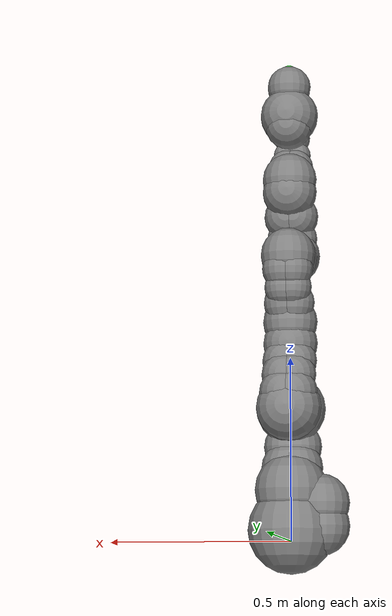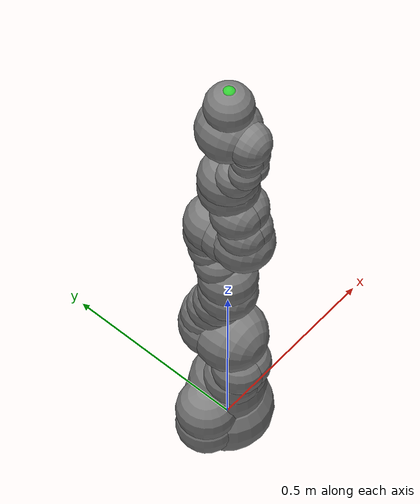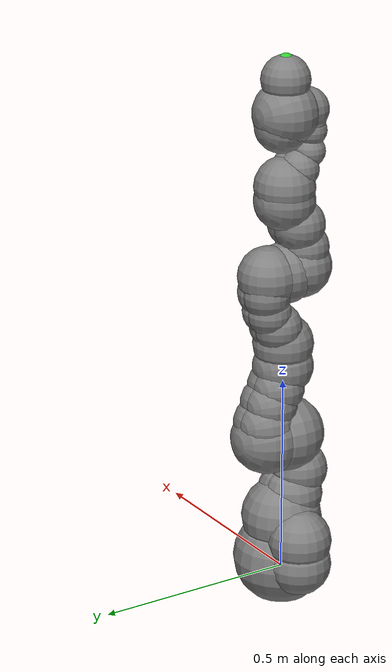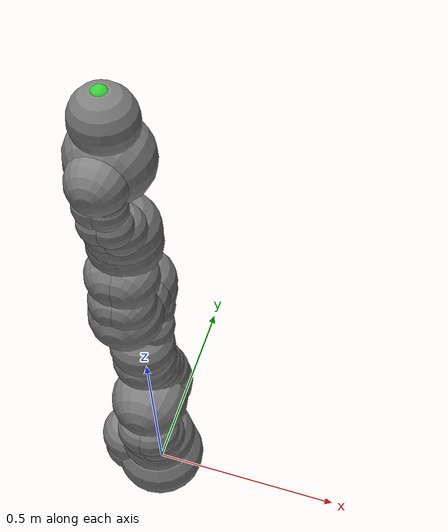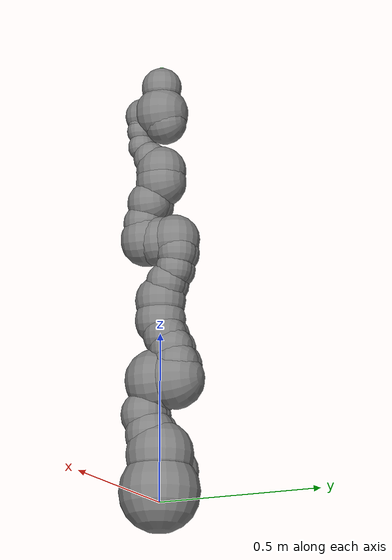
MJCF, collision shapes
<mujoco model="iiwa14">
  <compiler angle="radian" meshdir="assets" autolimits="true"/>

  <option integrator="implicitfast"/>

  <default>
    <default class="iiwa">
      <default class="visual">
        <geom type="mesh" contype="0" conaffinity="0" group="2" material="gray"/>
      </default>
      <default class="collision">
        <geom group="3"/>
      </default>
      <joint axis="0 0 1"/>
      <default class="joint1">
        <joint range="-2.96706 2.96706"/>
        <default class="joint2">
          <joint range="-2.0944 2.0944"/>
        </default>
      </default>
      <default class="joint3">
        <joint range="-3.05433 3.05433"/>
      </default>
    </default>
  </default>

  <asset>
    <material name="gray" rgba="0.4 0.4 0.4 1"/>
    <material name="light_gray" rgba="0.6 0.6 0.6 1"/>
    <material name="black" rgba="0 0 0 1"/>
    <material name="orange" rgba="1 0.423529 0.0392157 1"/>

    <mesh file="link_0.obj"/>
    <mesh file="link_1.obj"/>
    <mesh file="link_2_orange.obj"/>
    <mesh file="link_2_grey.obj"/>
    <mesh file="link_3.obj"/>
    <mesh file="band.obj"/>
    <mesh file="kuka.obj"/>
    <mesh file="link_4_orange.obj"/>
    <mesh file="link_4_grey.obj"/>
    <mesh file="link_5.obj"/>
    <mesh file="link_6_orange.obj"/>
    <mesh file="link_6_grey.obj"/>
    <mesh file="link_7.obj"/>
  </asset>

  <worldbody>
    <light name="top" pos="0 0 2" mode="trackcom"/>
    <body name="base" childclass="iiwa">
      <inertial mass="5" pos="-0.1 0 0.07" diaginertia="0.05 0.06 0.03"/>
      <geom name="base_visual" class="visual" mesh="link_0"/>
      <geom class="collision" size="0.12" pos="0 0 0.03"/>
      <geom class="collision" size="0.08" pos="-0.08 0 0.103"/>
      <geom class="collision" size="0.08" pos="-0.08 0 0.04"/>
      <geom class="collision" size="0.1" pos="0 0 0.14"/>
      <body name="link1" pos="0 0 0.1575">
        <site name="link1_dummy_site1" pos="0 0 0" quat="0 0 0 1" size="0.01" group="5"/>
        <site name="link1_dummy_site2" pos="0 0 0" quat="0 0 0 1" size="0.01" group="5"/>
        <site name="link1_dummy_site3" pos="0 0 0" quat="0 0 0 1" size="0.01" group="5"/>
        <site name="link1_dummy_site4" pos="0 0 0" quat="0 0 0 1" size="0.01" group="5"/>
        <site name="link1_dummy_site5" pos="0 0 0" quat="0 0 0 1" size="0.01" group="5"/>
        <site name="link1_dummy_site6" pos="0 0 0" quat="0 0 0 1" size="0.01" group="5"/>
        <site name="link1_dummy_site7" pos="0 0 0" quat="0 0 0 1" size="0.01" group="5"/>
        <site name="link1_dummy_site8" pos="0 0 0" quat="0 0 0 1" size="0.01" group="5"/>
        <site name="link1_dummy_site9" pos="0 0 0" quat="0 0 0 1" size="0.01" group="5"/>
        <site name="link1_dummy_site10" pos="0 0 0" quat="0 0 0 1" size="0.01" group="5"/>
        <site name="link1_dummy_site11" pos="0 0 0" quat="0 0 0 1" size="0.01" group="5"/>
        <site name="link1_dummy_site12" pos="0 0 0" quat="0 0 0 1" size="0.01" group="5"/>
        <site name="link1_dummy_site13" pos="0 0 0" quat="0 0 0 1" size="0.01" group="5"/>
        <site name="link1_dummy_site14" pos="0 0 0" quat="0 0 0 1" size="0.01" group="5"/>
        <site name="link1_dummy_site15" pos="0 0 0" quat="0 0 0 1" size="0.01" group="5"/>
        <site name="link1_dummy_site16" pos="0 0 0" quat="0 0 0 1" size="0.01" group="5"/>
        <site name="link1_dummy_site17" pos="0 0 0" quat="0 0 0 1" size="0.01" group="5"/>
        <site name="link1_dummy_site18" pos="0 0 0" quat="0 0 0 1" size="0.01" group="5"/>
        <site name="link1_dummy_site19" pos="0 0 0" quat="0 0 0 1" size="0.01" group="5"/>
        <site name="link1_dummy_site20" pos="0 0 0" quat="0 0 0 1" size="0.01" group="5"/>
        <site name="link1_dummy_site21" pos="0 0 0" quat="0 0 0 1" size="0.01" group="5"/>
        <site name="link1_dummy_site22" pos="0 0 0" quat="0 0 0 1" size="0.01" group="5"/>
        <site name="link1_dummy_site23" pos="0 0 0" quat="0 0 0 1" size="0.01" group="5"/>
        <site name="link1_dummy_site24" pos="0 0 0" quat="0 0 0 1" size="0.01" group="5"/>
        <site name="link1_dummy_site25" pos="0 0 0" quat="0 0 0 1" size="0.01" group="5"/>
        <site name="link1_dummy_site26" pos="0 0 0" quat="0 0 0 1" size="0.01" group="5"/>
        <site name="link1_dummy_site27" pos="0 0 0" quat="0 0 0 1" size="0.01" group="5"/>
        <site name="link1_dummy_site28" pos="0 0 0" quat="0 0 0 1" size="0.01" group="5"/>
        <site name="link1_dummy_site29" pos="0 0 0" quat="0 0 0 1" size="0.01" group="5"/>
        <site name="link1_dummy_site30" pos="0 0 0" quat="0 0 0 1" size="0.01" group="5"/>
        <site name="link1_dummy_site31" pos="0 0 0" quat="0 0 0 1" size="0.01" group="5"/>
        <site name="link1_dummy_site32" pos="0 0 0" quat="0 0 0 1" size="0.01" group="5"/>
        <site name="link1_dummy_site33" pos="0 0 0" quat="0 0 0 1" size="0.01" group="5"/>
        <site name="link1_dummy_site34" pos="0 0 0" quat="0 0 0 1" size="0.01" group="5"/>
        <site name="link1_dummy_site35" pos="0 0 0" quat="0 0 0 1" size="0.01" group="5"/>
        <site name="link1_dummy_site36" pos="0 0 0" quat="0 0 0 1" size="0.01" group="5"/>
        <site name="link1_dummy_site37" pos="0 0 0" quat="0 0 0 1" size="0.01" group="5"/>
        <site name="link1_dummy_site38" pos="0 0 0" quat="0 0 0 1" size="0.01" group="5"/>
        <site name="link1_dummy_site39" pos="0 0 0" quat="0 0 0 1" size="0.01" group="5"/>
        <site name="link1_dummy_site40" pos="0 0 0" quat="0 0 0 1" size="0.01" group="5"/>
        <site name="link1_dummy_site41" pos="0 0 0" quat="0 0 0 1" size="0.01" group="5"/>
        <site name="link1_dummy_site42" pos="0 0 0" quat="0 0 0 1" size="0.01" group="5"/>
        <site name="link1_dummy_site43" pos="0 0 0" quat="0 0 0 1" size="0.01" group="5"/>
        <site name="link1_dummy_site44" pos="0 0 0" quat="0 0 0 1" size="0.01" group="5"/>
        <site name="link1_dummy_site45" pos="0 0 0" quat="0 0 0 1" size="0.01" group="5"/>
        <site name="link1_dummy_site46" pos="0 0 0" quat="0 0 0 1" size="0.01" group="5"/>
        <site name="link1_dummy_site47" pos="0 0 0" quat="0 0 0 1" size="0.01" group="5"/>
        <site name="link1_dummy_site48" pos="0 0 0" quat="0 0 0 1" size="0.01" group="5"/>
        <site name="link1_dummy_site49" pos="0 0 0" quat="0 0 0 1" size="0.01" group="5"/>
        <site name="link1_dummy_site50" pos="0 0 0" quat="0 0 0 1" size="0.01" group="5"/>
        <site name="link1_dummy_site51" pos="0 0 0" quat="0 0 0 1" size="0.01" group="5"/>
        <site name="link1_dummy_site52" pos="0 0 0" quat="0 0 0 1" size="0.01" group="5"/>
        <site name="link1_dummy_site53" pos="0 0 0" quat="0 0 0 1" size="0.01" group="5"/>
        <site name="link1_dummy_site54" pos="0 0 0" quat="0 0 0 1" size="0.01" group="5"/>
        <site name="link1_dummy_site55" pos="0 0 0" quat="0 0 0 1" size="0.01" group="5"/>
        <site name="link1_dummy_site56" pos="0 0 0" quat="0 0 0 1" size="0.01" group="5"/>
        <site name="link1_dummy_site57" pos="0 0 0" quat="0 0 0 1" size="0.01" group="5"/>
        <site name="link1_dummy_site58" pos="0 0 0" quat="0 0 0 1" size="0.01" group="5"/>
        <site name="link1_dummy_site59" pos="0 0 0" quat="0 0 0 1" size="0.01" group="5"/>
        <site name="link1_dummy_site60" pos="0 0 0" quat="0 0 0 1" size="0.01" group="5"/>
        <site name="link1_dummy_site61" pos="0 0 0" quat="0 0 0 1" size="0.01" group="5"/>
        <site name="link1_dummy_site62" pos="0 0 0" quat="0 0 0 1" size="0.01" group="5"/>
        <site name="link1_dummy_site63" pos="0 0 0" quat="0 0 0 1" size="0.01" group="5"/>
        <site name="link1_dummy_site64" pos="0 0 0" quat="0 0 0 1" size="0.01" group="5"/>
        <site name="link1_dummy_site65" pos="0 0 0" quat="0 0 0 1" size="0.01" group="5"/>
        <site name="link1_dummy_site66" pos="0 0 0" quat="0 0 0 1" size="0.01" group="5"/>
        <site name="link1_dummy_site67" pos="0 0 0" quat="0 0 0 1" size="0.01" group="5"/>
        <site name="link1_dummy_site68" pos="0 0 0" quat="0 0 0 1" size="0.01" group="5"/>
        <site name="link1_dummy_site69" pos="0 0 0" quat="0 0 0 1" size="0.01" group="5"/>
        <site name="link1_dummy_site70" pos="0 0 0" quat="0 0 0 1" size="0.01" group="5"/>
        <site name="link1_dummy_site71" pos="0 0 0" quat="0 0 0 1" size="0.01" group="5"/>
        <site name="link1_dummy_site72" pos="0 0 0" quat="0 0 0 1" size="0.01" group="5"/>
        <site name="link1_dummy_site73" pos="0 0 0" quat="0 0 0 1" size="0.01" group="5"/>
        <site name="link1_dummy_site74" pos="0 0 0" quat="0 0 0 1" size="0.01" group="5"/>
        <site name="link1_dummy_site75" pos="0 0 0" quat="0 0 0 1" size="0.01" group="5"/>
        <site name="link1_dummy_site76" pos="0 0 0" quat="0 0 0 1" size="0.01" group="5"/>
        <site name="link1_dummy_site77" pos="0 0 0" quat="0 0 0 1" size="0.01" group="5"/>
        <site name="link1_dummy_site78" pos="0 0 0" quat="0 0 0 1" size="0.01" group="5"/>
        <site name="link1_dummy_site79" pos="0 0 0" quat="0 0 0 1" size="0.01" group="5"/>
        <site name="link1_dummy_site80" pos="0 0 0" quat="0 0 0 1" size="0.01" group="5"/>
        <site name="link1_dummy_site81" pos="0 0 0" quat="0 0 0 1" size="0.01" group="5"/>
        <site name="link1_dummy_site82" pos="0 0 0" quat="0 0 0 1" size="0.01" group="5"/>
        <site name="link1_dummy_site83" pos="0 0 0" quat="0 0 0 1" size="0.01" group="5"/>
        <site name="link1_dummy_site84" pos="0 0 0" quat="0 0 0 1" size="0.01" group="5"/>
        <site name="link1_dummy_site85" pos="0 0 0" quat="0 0 0 1" size="0.01" group="5"/>
        <site name="link1_dummy_site86" pos="0 0 0" quat="0 0 0 1" size="0.01" group="5"/>
        <site name="link1_dummy_site87" pos="0 0 0" quat="0 0 0 1" size="0.01" group="5"/>
        <site name="link1_dummy_site88" pos="0 0 0" quat="0 0 0 1" size="0.01" group="5"/>
        <site name="link1_dummy_site89" pos="0 0 0" quat="0 0 0 1" size="0.01" group="5"/>
        <site name="link1_dummy_site90" pos="0 0 0" quat="0 0 0 1" size="0.01" group="5"/>
        <site name="link1_dummy_site91" pos="0 0 0" quat="0 0 0 1" size="0.01" group="5"/>
        <site name="link1_dummy_site92" pos="0 0 0" quat="0 0 0 1" size="0.01" group="5"/>
        <site name="link1_dummy_site93" pos="0 0 0" quat="0 0 0 1" size="0.01" group="5"/>
        <site name="link1_dummy_site94" pos="0 0 0" quat="0 0 0 1" size="0.01" group="5"/>
        <site name="link1_dummy_site95" pos="0 0 0" quat="0 0 0 1" size="0.01" group="5"/>
        <site name="link1_dummy_site96" pos="0 0 0" quat="0 0 0 1" size="0.01" group="5"/>
        <site name="link1_dummy_site97" pos="0 0 0" quat="0 0 0 1" size="0.01" group="5"/>
        <site name="link1_dummy_site98" pos="0 0 0" quat="0 0 0 1" size="0.01" group="5"/>
        <site name="link1_dummy_site99" pos="0 0 0" quat="0 0 0 1" size="0.01" group="5"/>
        <site name="link1_dummy_site100" pos="0 0 0" quat="0 0 0 1" size="0.01" group="5"/>
        <site name="link1_dummy_site101" pos="0 0 0" quat="0 0 0 1" size="0.01" group="5"/>
        <site name="link1_dummy_site102" pos="0 0 0" quat="0 0 0 1" size="0.01" group="5"/>
        <site name="link1_dummy_site103" pos="0 0 0" quat="0 0 0 1" size="0.01" group="5"/>
        <site name="link1_dummy_site104" pos="0 0 0" quat="0 0 0 1" size="0.01" group="5"/>
        <site name="link1_dummy_site105" pos="0 0 0" quat="0 0 0 1" size="0.01" group="5"/>
        <site name="link1_dummy_site106" pos="0 0 0" quat="0 0 0 1" size="0.01" group="5"/>
        <site name="link1_dummy_site107" pos="0 0 0" quat="0 0 0 1" size="0.01" group="5"/>
        <site name="link1_dummy_site108" pos="0 0 0" quat="0 0 0 1" size="0.01" group="5"/>
        <site name="link1_dummy_site109" pos="0 0 0" quat="0 0 0 1" size="0.01" group="5"/>
        <site name="link1_dummy_site110" pos="0 0 0" quat="0 0 0 1" size="0.01" group="5"/>
        <site name="link1_dummy_site111" pos="0 0 0" quat="0 0 0 1" size="0.01" group="5"/>
        <site name="link1_dummy_site112" pos="0 0 0" quat="0 0 0 1" size="0.01" group="5"/>
        <site name="link1_dummy_site113" pos="0 0 0" quat="0 0 0 1" size="0.01" group="5"/>
        <site name="link1_dummy_site114" pos="0 0 0" quat="0 0 0 1" size="0.01" group="5"/>
        <site name="link1_dummy_site115" pos="0 0 0" quat="0 0 0 1" size="0.01" group="5"/>
        <site name="link1_dummy_site116" pos="0 0 0" quat="0 0 0 1" size="0.01" group="5"/>
        <site name="link1_dummy_site117" pos="0 0 0" quat="0 0 0 1" size="0.01" group="5"/>
        <site name="link1_dummy_site118" pos="0 0 0" quat="0 0 0 1" size="0.01" group="5"/>
        <site name="link1_dummy_site119" pos="0 0 0" quat="0 0 0 1" size="0.01" group="5"/>
        <site name="link1_dummy_site120" pos="0 0 0" quat="0 0 0 1" size="0.01" group="5"/>
        <site name="link1_dummy_site121" pos="0 0 0" quat="0 0 0 1" size="0.01" group="5"/>
        <site name="link1_dummy_site122" pos="0 0 0" quat="0 0 0 1" size="0.01" group="5"/>
        <site name="link1_dummy_site123" pos="0 0 0" quat="0 0 0 1" size="0.01" group="5"/>
        <site name="link1_dummy_site124" pos="0 0 0" quat="0 0 0 1" size="0.01" group="5"/>
        <site name="link1_dummy_site125" pos="0 0 0" quat="0 0 0 1" size="0.01" group="5"/>
        <site name="link1_dummy_site126" pos="0 0 0" quat="0 0 0 1" size="0.01" group="5"/>
        <site name="link1_dummy_site127" pos="0 0 0" quat="0 0 0 1" size="0.01" group="5"/>
        <site name="link1_dummy_site128" pos="0 0 0" quat="0 0 0 1" size="0.01" group="5"/>
        <site name="link1_dummy_site129" pos="0 0 0" quat="0 0 0 1" size="0.01" group="5"/>
        <site name="link1_dummy_site130" pos="0 0 0" quat="0 0 0 1" size="0.01" group="5"/>
        <site name="link1_dummy_site131" pos="0 0 0" quat="0 0 0 1" size="0.01" group="5"/>
        <site name="link1_dummy_site132" pos="0 0 0" quat="0 0 0 1" size="0.01" group="5"/>
        <site name="link1_dummy_site133" pos="0 0 0" quat="0 0 0 1" size="0.01" group="5"/>
        <site name="link1_dummy_site134" pos="0 0 0" quat="0 0 0 1" size="0.01" group="5"/>
        <site name="link1_dummy_site135" pos="0 0 0" quat="0 0 0 1" size="0.01" group="5"/>
        <site name="link1_dummy_site136" pos="0 0 0" quat="0 0 0 1" size="0.01" group="5"/>
        <site name="link1_dummy_site137" pos="0 0 0" quat="0 0 0 1" size="0.01" group="5"/>
        <site name="link1_dummy_site138" pos="0 0 0" quat="0 0 0 1" size="0.01" group="5"/>
        <site name="link1_dummy_site139" pos="0 0 0" quat="0 0 0 1" size="0.01" group="5"/>
        <site name="link1_dummy_site140" pos="0 0 0" quat="0 0 0 1" size="0.01" group="5"/>
        <site name="link1_dummy_site141" pos="0 0 0" quat="0 0 0 1" size="0.01" group="5"/>
        <site name="link1_dummy_site142" pos="0 0 0" quat="0 0 0 1" size="0.01" group="5"/>
        <site name="link1_dummy_site143" pos="0 0 0" quat="0 0 0 1" size="0.01" group="5"/>
        <site name="link1_dummy_site144" pos="0 0 0" quat="0 0 0 1" size="0.01" group="5"/>
        <site name="link1_dummy_site145" pos="0 0 0" quat="0 0 0 1" size="0.01" group="5"/>
        <site name="link1_dummy_site146" pos="0 0 0" quat="0 0 0 1" size="0.01" group="5"/>
        <site name="link1_dummy_site147" pos="0 0 0" quat="0 0 0 1" size="0.01" group="5"/>
        <site name="link1_dummy_site148" pos="0 0 0" quat="0 0 0 1" size="0.01" group="5"/>
        <site name="link1_dummy_site149" pos="0 0 0" quat="0 0 0 1" size="0.01" group="5"/>
        <site name="link1_dummy_site150" pos="0 0 0" quat="0 0 0 1" size="0.01" group="5"/>
        <site name="link1_dummy_site151" pos="0 0 0" quat="0 0 0 1" size="0.01" group="5"/>
        <site name="link1_dummy_site152" pos="0 0 0" quat="0 0 0 1" size="0.01" group="5"/>
        <site name="link1_dummy_site153" pos="0 0 0" quat="0 0 0 1" size="0.01" group="5"/>
        <site name="link1_dummy_site154" pos="0 0 0" quat="0 0 0 1" size="0.01" group="5"/>
        <site name="link1_dummy_site155" pos="0 0 0" quat="0 0 0 1" size="0.01" group="5"/>
        <site name="link1_dummy_site156" pos="0 0 0" quat="0 0 0 1" size="0.01" group="5"/>
        <site name="link1_dummy_site157" pos="0 0 0" quat="0 0 0 1" size="0.01" group="5"/>
        <site name="link1_dummy_site158" pos="0 0 0" quat="0 0 0 1" size="0.01" group="5"/>
        <site name="link1_dummy_site159" pos="0 0 0" quat="0 0 0 1" size="0.01" group="5"/>
        <site name="link1_dummy_site160" pos="0 0 0" quat="0 0 0 1" size="0.01" group="5"/>
        <site name="link1_dummy_site161" pos="0 0 0" quat="0 0 0 1" size="0.01" group="5"/>
        <site name="link1_dummy_site162" pos="0 0 0" quat="0 0 0 1" size="0.01" group="5"/>
        <site name="link1_dummy_site163" pos="0 0 0" quat="0 0 0 1" size="0.01" group="5"/>
        <site name="link1_dummy_site164" pos="0 0 0" quat="0 0 0 1" size="0.01" group="5"/>
        <site name="link1_dummy_site165" pos="0 0 0" quat="0 0 0 1" size="0.01" group="5"/>
        <site name="link1_dummy_site166" pos="0 0 0" quat="0 0 0 1" size="0.01" group="5"/>
        <site name="link1_dummy_site167" pos="0 0 0" quat="0 0 0 1" size="0.01" group="5"/>
        <site name="link1_dummy_site168" pos="0 0 0" quat="0 0 0 1" size="0.01" group="5"/>
        <site name="link1_dummy_site169" pos="0 0 0" quat="0 0 0 1" size="0.01" group="5"/>
        <site name="link1_dummy_site170" pos="0 0 0" quat="0 0 0 1" size="0.01" group="5"/>
        <site name="link1_dummy_site171" pos="0 0 0" quat="0 0 0 1" size="0.01" group="5"/>
        <site name="link1_dummy_site172" pos="0 0 0" quat="0 0 0 1" size="0.01" group="5"/>
        <site name="link1_dummy_site173" pos="0 0 0" quat="0 0 0 1" size="0.01" group="5"/>
        <site name="link1_dummy_site174" pos="0 0 0" quat="0 0 0 1" size="0.01" group="5"/>
        <site name="link1_dummy_site175" pos="0 0 0" quat="0 0 0 1" size="0.01" group="5"/>
        <site name="link1_dummy_site176" pos="0 0 0" quat="0 0 0 1" size="0.01" group="5"/>
        <site name="link1_dummy_site177" pos="0 0 0" quat="0 0 0 1" size="0.01" group="5"/>
        <site name="link1_dummy_site178" pos="0 0 0" quat="0 0 0 1" size="0.01" group="5"/>
        <site name="link1_dummy_site179" pos="0 0 0" quat="0 0 0 1" size="0.01" group="5"/>
        <site name="link1_dummy_site180" pos="0 0 0" quat="0 0 0 1" size="0.01" group="5"/>
        <site name="link1_dummy_site181" pos="0 0 0" quat="0 0 0 1" size="0.01" group="5"/>
        <site name="link1_dummy_site182" pos="0 0 0" quat="0 0 0 1" size="0.01" group="5"/>
        <site name="link1_dummy_site183" pos="0 0 0" quat="0 0 0 1" size="0.01" group="5"/>
        <site name="link1_dummy_site184" pos="0 0 0" quat="0 0 0 1" size="0.01" group="5"/>
        <site name="link1_dummy_site185" pos="0 0 0" quat="0 0 0 1" size="0.01" group="5"/>
        <site name="link1_dummy_site186" pos="0 0 0" quat="0 0 0 1" size="0.01" group="5"/>
        <site name="link1_dummy_site187" pos="0 0 0" quat="0 0 0 1" size="0.01" group="5"/>
        <site name="link1_dummy_site188" pos="0 0 0" quat="0 0 0 1" size="0.01" group="5"/>
        <site name="link1_dummy_site189" pos="0 0 0" quat="0 0 0 1" size="0.01" group="5"/>
        <site name="link1_dummy_site190" pos="0 0 0" quat="0 0 0 1" size="0.01" group="5"/>
        <site name="link1_dummy_site191" pos="0 0 0" quat="0 0 0 1" size="0.01" group="5"/>
        <site name="link1_dummy_site192" pos="0 0 0" quat="0 0 0 1" size="0.01" group="5"/>
        <site name="link1_dummy_site193" pos="0 0 0" quat="0 0 0 1" size="0.01" group="5"/>
        <site name="link1_dummy_site194" pos="0 0 0" quat="0 0 0 1" size="0.01" group="5"/>
        <site name="link1_dummy_site195" pos="0 0 0" quat="0 0 0 1" size="0.01" group="5"/>
        <site name="link1_dummy_site196" pos="0 0 0" quat="0 0 0 1" size="0.01" group="5"/>
        <site name="link1_dummy_site197" pos="0 0 0" quat="0 0 0 1" size="0.01" group="5"/>
        <site name="link1_dummy_site198" pos="0 0 0" quat="0 0 0 1" size="0.01" group="5"/>
        <site name="link1_dummy_site199" pos="0 0 0" quat="0 0 0 1" size="0.01" group="5"/>
        <site name="link1_dummy_site200" pos="0 0 0" quat="0 0 0 1" size="0.01" group="5"/>
        <site name="link1_dummy_site201" pos="0 0 0" quat="0 0 0 1" size="0.01" group="5"/>
        <inertial mass="5.76" pos="0 -0.03 0.12" diaginertia="0.0333 0.033 0.0123"/>
        <joint name="joint1" class="joint1"/>
        <geom name="link1_visual" class="visual" mesh="link_1"/>
        <geom class="collision" size="0.08" pos="0 0 -0.0005"/>
        <geom class="collision" size="0.075" pos="0.01 -0.025 0.0425"/>
        <geom class="collision" size="0.075" pos="-0.01 -0.025 0.0425"/>
        <geom class="collision" size="0.07" pos="0.01 -0.045 0.1025"/>
        <geom class="collision" size="0.07" pos="-0.01 -0.045 0.1025"/>
        <body name="link2" pos="0 0 0.2025" quat="0 0 1 1">
          <site name="link2_dummy_site1" pos="0 0 0" quat="0 0 0 1" size="0.01" group="5"/>
          <site name="link2_dummy_site2" pos="0 0 0" quat="0 0 0 1" size="0.01" group="5"/>
          <site name="link2_dummy_site3" pos="0 0 0" quat="0 0 0 1" size="0.01" group="5"/>
          <site name="link2_dummy_site4" pos="0 0 0" quat="0 0 0 1" size="0.01" group="5"/>
          <site name="link2_dummy_site5" pos="0 0 0" quat="0 0 0 1" size="0.01" group="5"/>
          <site name="link2_dummy_site6" pos="0 0 0" quat="0 0 0 1" size="0.01" group="5"/>
          <site name="link2_dummy_site7" pos="0 0 0" quat="0 0 0 1" size="0.01" group="5"/>
          <site name="link2_dummy_site8" pos="0 0 0" quat="0 0 0 1" size="0.01" group="5"/>
          <site name="link2_dummy_site9" pos="0 0 0" quat="0 0 0 1" size="0.01" group="5"/>
          <site name="link2_dummy_site10" pos="0 0 0" quat="0 0 0 1" size="0.01" group="5"/>
          <site name="link2_dummy_site11" pos="0 0 0" quat="0 0 0 1" size="0.01" group="5"/>
          <site name="link2_dummy_site12" pos="0 0 0" quat="0 0 0 1" size="0.01" group="5"/>
          <site name="link2_dummy_site13" pos="0 0 0" quat="0 0 0 1" size="0.01" group="5"/>
          <site name="link2_dummy_site14" pos="0 0 0" quat="0 0 0 1" size="0.01" group="5"/>
          <site name="link2_dummy_site15" pos="0 0 0" quat="0 0 0 1" size="0.01" group="5"/>
          <site name="link2_dummy_site16" pos="0 0 0" quat="0 0 0 1" size="0.01" group="5"/>
          <site name="link2_dummy_site17" pos="0 0 0" quat="0 0 0 1" size="0.01" group="5"/>
          <site name="link2_dummy_site18" pos="0 0 0" quat="0 0 0 1" size="0.01" group="5"/>
          <site name="link2_dummy_site19" pos="0 0 0" quat="0 0 0 1" size="0.01" group="5"/>
          <site name="link2_dummy_site20" pos="0 0 0" quat="0 0 0 1" size="0.01" group="5"/>
          <site name="link2_dummy_site21" pos="0 0 0" quat="0 0 0 1" size="0.01" group="5"/>
          <site name="link2_dummy_site22" pos="0 0 0" quat="0 0 0 1" size="0.01" group="5"/>
          <site name="link2_dummy_site23" pos="0 0 0" quat="0 0 0 1" size="0.01" group="5"/>
          <site name="link2_dummy_site24" pos="0 0 0" quat="0 0 0 1" size="0.01" group="5"/>
          <site name="link2_dummy_site25" pos="0 0 0" quat="0 0 0 1" size="0.01" group="5"/>
          <site name="link2_dummy_site26" pos="0 0 0" quat="0 0 0 1" size="0.01" group="5"/>
          <site name="link2_dummy_site27" pos="0 0 0" quat="0 0 0 1" size="0.01" group="5"/>
          <site name="link2_dummy_site28" pos="0 0 0" quat="0 0 0 1" size="0.01" group="5"/>
          <site name="link2_dummy_site29" pos="0 0 0" quat="0 0 0 1" size="0.01" group="5"/>
          <site name="link2_dummy_site30" pos="0 0 0" quat="0 0 0 1" size="0.01" group="5"/>
          <site name="link2_dummy_site31" pos="0 0 0" quat="0 0 0 1" size="0.01" group="5"/>
          <site name="link2_dummy_site32" pos="0 0 0" quat="0 0 0 1" size="0.01" group="5"/>
          <site name="link2_dummy_site33" pos="0 0 0" quat="0 0 0 1" size="0.01" group="5"/>
          <site name="link2_dummy_site34" pos="0 0 0" quat="0 0 0 1" size="0.01" group="5"/>
          <site name="link2_dummy_site35" pos="0 0 0" quat="0 0 0 1" size="0.01" group="5"/>
          <site name="link2_dummy_site36" pos="0 0 0" quat="0 0 0 1" size="0.01" group="5"/>
          <site name="link2_dummy_site37" pos="0 0 0" quat="0 0 0 1" size="0.01" group="5"/>
          <site name="link2_dummy_site38" pos="0 0 0" quat="0 0 0 1" size="0.01" group="5"/>
          <site name="link2_dummy_site39" pos="0 0 0" quat="0 0 0 1" size="0.01" group="5"/>
          <site name="link2_dummy_site40" pos="0 0 0" quat="0 0 0 1" size="0.01" group="5"/>
          <site name="link2_dummy_site41" pos="0 0 0" quat="0 0 0 1" size="0.01" group="5"/>
          <site name="link2_dummy_site42" pos="0 0 0" quat="0 0 0 1" size="0.01" group="5"/>
          <site name="link2_dummy_site43" pos="0 0 0" quat="0 0 0 1" size="0.01" group="5"/>
          <site name="link2_dummy_site44" pos="0 0 0" quat="0 0 0 1" size="0.01" group="5"/>
          <site name="link2_dummy_site45" pos="0 0 0" quat="0 0 0 1" size="0.01" group="5"/>
          <site name="link2_dummy_site46" pos="0 0 0" quat="0 0 0 1" size="0.01" group="5"/>
          <site name="link2_dummy_site47" pos="0 0 0" quat="0 0 0 1" size="0.01" group="5"/>
          <site name="link2_dummy_site48" pos="0 0 0" quat="0 0 0 1" size="0.01" group="5"/>
          <site name="link2_dummy_site49" pos="0 0 0" quat="0 0 0 1" size="0.01" group="5"/>
          <site name="link2_dummy_site50" pos="0 0 0" quat="0 0 0 1" size="0.01" group="5"/>
          <site name="link2_dummy_site51" pos="0 0 0" quat="0 0 0 1" size="0.01" group="5"/>
          <site name="link2_dummy_site52" pos="0 0 0" quat="0 0 0 1" size="0.01" group="5"/>
          <site name="link2_dummy_site53" pos="0 0 0" quat="0 0 0 1" size="0.01" group="5"/>
          <site name="link2_dummy_site54" pos="0 0 0" quat="0 0 0 1" size="0.01" group="5"/>
          <site name="link2_dummy_site55" pos="0 0 0" quat="0 0 0 1" size="0.01" group="5"/>
          <site name="link2_dummy_site56" pos="0 0 0" quat="0 0 0 1" size="0.01" group="5"/>
          <site name="link2_dummy_site57" pos="0 0 0" quat="0 0 0 1" size="0.01" group="5"/>
          <site name="link2_dummy_site58" pos="0 0 0" quat="0 0 0 1" size="0.01" group="5"/>
          <site name="link2_dummy_site59" pos="0 0 0" quat="0 0 0 1" size="0.01" group="5"/>
          <site name="link2_dummy_site60" pos="0 0 0" quat="0 0 0 1" size="0.01" group="5"/>
          <site name="link2_dummy_site61" pos="0 0 0" quat="0 0 0 1" size="0.01" group="5"/>
          <site name="link2_dummy_site62" pos="0 0 0" quat="0 0 0 1" size="0.01" group="5"/>
          <site name="link2_dummy_site63" pos="0 0 0" quat="0 0 0 1" size="0.01" group="5"/>
          <site name="link2_dummy_site64" pos="0 0 0" quat="0 0 0 1" size="0.01" group="5"/>
          <site name="link2_dummy_site65" pos="0 0 0" quat="0 0 0 1" size="0.01" group="5"/>
          <site name="link2_dummy_site66" pos="0 0 0" quat="0 0 0 1" size="0.01" group="5"/>
          <site name="link2_dummy_site67" pos="0 0 0" quat="0 0 0 1" size="0.01" group="5"/>
          <site name="link2_dummy_site68" pos="0 0 0" quat="0 0 0 1" size="0.01" group="5"/>
          <site name="link2_dummy_site69" pos="0 0 0" quat="0 0 0 1" size="0.01" group="5"/>
          <site name="link2_dummy_site70" pos="0 0 0" quat="0 0 0 1" size="0.01" group="5"/>
          <site name="link2_dummy_site71" pos="0 0 0" quat="0 0 0 1" size="0.01" group="5"/>
          <site name="link2_dummy_site72" pos="0 0 0" quat="0 0 0 1" size="0.01" group="5"/>
          <site name="link2_dummy_site73" pos="0 0 0" quat="0 0 0 1" size="0.01" group="5"/>
          <site name="link2_dummy_site74" pos="0 0 0" quat="0 0 0 1" size="0.01" group="5"/>
          <site name="link2_dummy_site75" pos="0 0 0" quat="0 0 0 1" size="0.01" group="5"/>
          <site name="link2_dummy_site76" pos="0 0 0" quat="0 0 0 1" size="0.01" group="5"/>
          <site name="link2_dummy_site77" pos="0 0 0" quat="0 0 0 1" size="0.01" group="5"/>
          <site name="link2_dummy_site78" pos="0 0 0" quat="0 0 0 1" size="0.01" group="5"/>
          <site name="link2_dummy_site79" pos="0 0 0" quat="0 0 0 1" size="0.01" group="5"/>
          <site name="link2_dummy_site80" pos="0 0 0" quat="0 0 0 1" size="0.01" group="5"/>
          <site name="link2_dummy_site81" pos="0 0 0" quat="0 0 0 1" size="0.01" group="5"/>
          <site name="link2_dummy_site82" pos="0 0 0" quat="0 0 0 1" size="0.01" group="5"/>
          <site name="link2_dummy_site83" pos="0 0 0" quat="0 0 0 1" size="0.01" group="5"/>
          <site name="link2_dummy_site84" pos="0 0 0" quat="0 0 0 1" size="0.01" group="5"/>
          <site name="link2_dummy_site85" pos="0 0 0" quat="0 0 0 1" size="0.01" group="5"/>
          <site name="link2_dummy_site86" pos="0 0 0" quat="0 0 0 1" size="0.01" group="5"/>
          <site name="link2_dummy_site87" pos="0 0 0" quat="0 0 0 1" size="0.01" group="5"/>
          <site name="link2_dummy_site88" pos="0 0 0" quat="0 0 0 1" size="0.01" group="5"/>
          <site name="link2_dummy_site89" pos="0 0 0" quat="0 0 0 1" size="0.01" group="5"/>
          <site name="link2_dummy_site90" pos="0 0 0" quat="0 0 0 1" size="0.01" group="5"/>
          <site name="link2_dummy_site91" pos="0 0 0" quat="0 0 0 1" size="0.01" group="5"/>
          <site name="link2_dummy_site92" pos="0 0 0" quat="0 0 0 1" size="0.01" group="5"/>
          <site name="link2_dummy_site93" pos="0 0 0" quat="0 0 0 1" size="0.01" group="5"/>
          <site name="link2_dummy_site94" pos="0 0 0" quat="0 0 0 1" size="0.01" group="5"/>
          <site name="link2_dummy_site95" pos="0 0 0" quat="0 0 0 1" size="0.01" group="5"/>
          <site name="link2_dummy_site96" pos="0 0 0" quat="0 0 0 1" size="0.01" group="5"/>
          <site name="link2_dummy_site97" pos="0 0 0" quat="0 0 0 1" size="0.01" group="5"/>
          <site name="link2_dummy_site98" pos="0 0 0" quat="0 0 0 1" size="0.01" group="5"/>
          <site name="link2_dummy_site99" pos="0 0 0" quat="0 0 0 1" size="0.01" group="5"/>
          <site name="link2_dummy_site100" pos="0 0 0" quat="0 0 0 1" size="0.01" group="5"/>
          <site name="link2_dummy_site101" pos="0 0 0" quat="0 0 0 1" size="0.01" group="5"/>
          <site name="link2_dummy_site102" pos="0 0 0" quat="0 0 0 1" size="0.01" group="5"/>
          <site name="link2_dummy_site103" pos="0 0 0" quat="0 0 0 1" size="0.01" group="5"/>
          <site name="link2_dummy_site104" pos="0 0 0" quat="0 0 0 1" size="0.01" group="5"/>
          <site name="link2_dummy_site105" pos="0 0 0" quat="0 0 0 1" size="0.01" group="5"/>
          <site name="link2_dummy_site106" pos="0 0 0" quat="0 0 0 1" size="0.01" group="5"/>
          <site name="link2_dummy_site107" pos="0 0 0" quat="0 0 0 1" size="0.01" group="5"/>
          <site name="link2_dummy_site108" pos="0 0 0" quat="0 0 0 1" size="0.01" group="5"/>
          <site name="link2_dummy_site109" pos="0 0 0" quat="0 0 0 1" size="0.01" group="5"/>
          <site name="link2_dummy_site110" pos="0 0 0" quat="0 0 0 1" size="0.01" group="5"/>
          <site name="link2_dummy_site111" pos="0 0 0" quat="0 0 0 1" size="0.01" group="5"/>
          <site name="link2_dummy_site112" pos="0 0 0" quat="0 0 0 1" size="0.01" group="5"/>
          <site name="link2_dummy_site113" pos="0 0 0" quat="0 0 0 1" size="0.01" group="5"/>
          <site name="link2_dummy_site114" pos="0 0 0" quat="0 0 0 1" size="0.01" group="5"/>
          <site name="link2_dummy_site115" pos="0 0 0" quat="0 0 0 1" size="0.01" group="5"/>
          <site name="link2_dummy_site116" pos="0 0 0" quat="0 0 0 1" size="0.01" group="5"/>
          <site name="link2_dummy_site117" pos="0 0 0" quat="0 0 0 1" size="0.01" group="5"/>
          <site name="link2_dummy_site118" pos="0 0 0" quat="0 0 0 1" size="0.01" group="5"/>
          <site name="link2_dummy_site119" pos="0 0 0" quat="0 0 0 1" size="0.01" group="5"/>
          <site name="link2_dummy_site120" pos="0 0 0" quat="0 0 0 1" size="0.01" group="5"/>
          <site name="link2_dummy_site121" pos="0 0 0" quat="0 0 0 1" size="0.01" group="5"/>
          <site name="link2_dummy_site122" pos="0 0 0" quat="0 0 0 1" size="0.01" group="5"/>
          <site name="link2_dummy_site123" pos="0 0 0" quat="0 0 0 1" size="0.01" group="5"/>
          <site name="link2_dummy_site124" pos="0 0 0" quat="0 0 0 1" size="0.01" group="5"/>
          <site name="link2_dummy_site125" pos="0 0 0" quat="0 0 0 1" size="0.01" group="5"/>
          <site name="link2_dummy_site126" pos="0 0 0" quat="0 0 0 1" size="0.01" group="5"/>
          <site name="link2_dummy_site127" pos="0 0 0" quat="0 0 0 1" size="0.01" group="5"/>
          <site name="link2_dummy_site128" pos="0 0 0" quat="0 0 0 1" size="0.01" group="5"/>
          <site name="link2_dummy_site129" pos="0 0 0" quat="0 0 0 1" size="0.01" group="5"/>
          <site name="link2_dummy_site130" pos="0 0 0" quat="0 0 0 1" size="0.01" group="5"/>
          <site name="link2_dummy_site131" pos="0 0 0" quat="0 0 0 1" size="0.01" group="5"/>
          <site name="link2_dummy_site132" pos="0 0 0" quat="0 0 0 1" size="0.01" group="5"/>
          <site name="link2_dummy_site133" pos="0 0 0" quat="0 0 0 1" size="0.01" group="5"/>
          <site name="link2_dummy_site134" pos="0 0 0" quat="0 0 0 1" size="0.01" group="5"/>
          <site name="link2_dummy_site135" pos="0 0 0" quat="0 0 0 1" size="0.01" group="5"/>
          <site name="link2_dummy_site136" pos="0 0 0" quat="0 0 0 1" size="0.01" group="5"/>
          <site name="link2_dummy_site137" pos="0 0 0" quat="0 0 0 1" size="0.01" group="5"/>
          <site name="link2_dummy_site138" pos="0 0 0" quat="0 0 0 1" size="0.01" group="5"/>
          <site name="link2_dummy_site139" pos="0 0 0" quat="0 0 0 1" size="0.01" group="5"/>
          <site name="link2_dummy_site140" pos="0 0 0" quat="0 0 0 1" size="0.01" group="5"/>
          <site name="link2_dummy_site141" pos="0 0 0" quat="0 0 0 1" size="0.01" group="5"/>
          <site name="link2_dummy_site142" pos="0 0 0" quat="0 0 0 1" size="0.01" group="5"/>
          <site name="link2_dummy_site143" pos="0 0 0" quat="0 0 0 1" size="0.01" group="5"/>
          <site name="link2_dummy_site144" pos="0 0 0" quat="0 0 0 1" size="0.01" group="5"/>
          <site name="link2_dummy_site145" pos="0 0 0" quat="0 0 0 1" size="0.01" group="5"/>
          <site name="link2_dummy_site146" pos="0 0 0" quat="0 0 0 1" size="0.01" group="5"/>
          <site name="link2_dummy_site147" pos="0 0 0" quat="0 0 0 1" size="0.01" group="5"/>
          <site name="link2_dummy_site148" pos="0 0 0" quat="0 0 0 1" size="0.01" group="5"/>
          <site name="link2_dummy_site149" pos="0 0 0" quat="0 0 0 1" size="0.01" group="5"/>
          <site name="link2_dummy_site150" pos="0 0 0" quat="0 0 0 1" size="0.01" group="5"/>
          <site name="link2_dummy_site151" pos="0 0 0" quat="0 0 0 1" size="0.01" group="5"/>
          <site name="link2_dummy_site152" pos="0 0 0" quat="0 0 0 1" size="0.01" group="5"/>
          <site name="link2_dummy_site153" pos="0 0 0" quat="0 0 0 1" size="0.01" group="5"/>
          <site name="link2_dummy_site154" pos="0 0 0" quat="0 0 0 1" size="0.01" group="5"/>
          <site name="link2_dummy_site155" pos="0 0 0" quat="0 0 0 1" size="0.01" group="5"/>
          <site name="link2_dummy_site156" pos="0 0 0" quat="0 0 0 1" size="0.01" group="5"/>
          <site name="link2_dummy_site157" pos="0 0 0" quat="0 0 0 1" size="0.01" group="5"/>
          <site name="link2_dummy_site158" pos="0 0 0" quat="0 0 0 1" size="0.01" group="5"/>
          <site name="link2_dummy_site159" pos="0 0 0" quat="0 0 0 1" size="0.01" group="5"/>
          <site name="link2_dummy_site160" pos="0 0 0" quat="0 0 0 1" size="0.01" group="5"/>
          <site name="link2_dummy_site161" pos="0 0 0" quat="0 0 0 1" size="0.01" group="5"/>
          <site name="link2_dummy_site162" pos="0 0 0" quat="0 0 0 1" size="0.01" group="5"/>
          <site name="link2_dummy_site163" pos="0 0 0" quat="0 0 0 1" size="0.01" group="5"/>
          <site name="link2_dummy_site164" pos="0 0 0" quat="0 0 0 1" size="0.01" group="5"/>
          <site name="link2_dummy_site165" pos="0 0 0" quat="0 0 0 1" size="0.01" group="5"/>
          <site name="link2_dummy_site166" pos="0 0 0" quat="0 0 0 1" size="0.01" group="5"/>
          <site name="link2_dummy_site167" pos="0 0 0" quat="0 0 0 1" size="0.01" group="5"/>
          <site name="link2_dummy_site168" pos="0 0 0" quat="0 0 0 1" size="0.01" group="5"/>
          <site name="link2_dummy_site169" pos="0 0 0" quat="0 0 0 1" size="0.01" group="5"/>
          <site name="link2_dummy_site170" pos="0 0 0" quat="0 0 0 1" size="0.01" group="5"/>
          <site name="link2_dummy_site171" pos="0 0 0" quat="0 0 0 1" size="0.01" group="5"/>
          <site name="link2_dummy_site172" pos="0 0 0" quat="0 0 0 1" size="0.01" group="5"/>
          <site name="link2_dummy_site173" pos="0 0 0" quat="0 0 0 1" size="0.01" group="5"/>
          <site name="link2_dummy_site174" pos="0 0 0" quat="0 0 0 1" size="0.01" group="5"/>
          <site name="link2_dummy_site175" pos="0 0 0" quat="0 0 0 1" size="0.01" group="5"/>
          <site name="link2_dummy_site176" pos="0 0 0" quat="0 0 0 1" size="0.01" group="5"/>
          <site name="link2_dummy_site177" pos="0 0 0" quat="0 0 0 1" size="0.01" group="5"/>
          <site name="link2_dummy_site178" pos="0 0 0" quat="0 0 0 1" size="0.01" group="5"/>
          <site name="link2_dummy_site179" pos="0 0 0" quat="0 0 0 1" size="0.01" group="5"/>
          <site name="link2_dummy_site180" pos="0 0 0" quat="0 0 0 1" size="0.01" group="5"/>
          <site name="link2_dummy_site181" pos="0 0 0" quat="0 0 0 1" size="0.01" group="5"/>
          <site name="link2_dummy_site182" pos="0 0 0" quat="0 0 0 1" size="0.01" group="5"/>
          <site name="link2_dummy_site183" pos="0 0 0" quat="0 0 0 1" size="0.01" group="5"/>
          <site name="link2_dummy_site184" pos="0 0 0" quat="0 0 0 1" size="0.01" group="5"/>
          <site name="link2_dummy_site185" pos="0 0 0" quat="0 0 0 1" size="0.01" group="5"/>
          <site name="link2_dummy_site186" pos="0 0 0" quat="0 0 0 1" size="0.01" group="5"/>
          <site name="link2_dummy_site187" pos="0 0 0" quat="0 0 0 1" size="0.01" group="5"/>
          <site name="link2_dummy_site188" pos="0 0 0" quat="0 0 0 1" size="0.01" group="5"/>
          <site name="link2_dummy_site189" pos="0 0 0" quat="0 0 0 1" size="0.01" group="5"/>
          <site name="link2_dummy_site190" pos="0 0 0" quat="0 0 0 1" size="0.01" group="5"/>
          <site name="link2_dummy_site191" pos="0 0 0" quat="0 0 0 1" size="0.01" group="5"/>
          <site name="link2_dummy_site192" pos="0 0 0" quat="0 0 0 1" size="0.01" group="5"/>
          <site name="link2_dummy_site193" pos="0 0 0" quat="0 0 0 1" size="0.01" group="5"/>
          <site name="link2_dummy_site194" pos="0 0 0" quat="0 0 0 1" size="0.01" group="5"/>
          <site name="link2_dummy_site195" pos="0 0 0" quat="0 0 0 1" size="0.01" group="5"/>
          <site name="link2_dummy_site196" pos="0 0 0" quat="0 0 0 1" size="0.01" group="5"/>
          <site name="link2_dummy_site197" pos="0 0 0" quat="0 0 0 1" size="0.01" group="5"/>
          <site name="link2_dummy_site198" pos="0 0 0" quat="0 0 0 1" size="0.01" group="5"/>
          <site name="link2_dummy_site199" pos="0 0 0" quat="0 0 0 1" size="0.01" group="5"/>
          <site name="link2_dummy_site200" pos="0 0 0" quat="0 0 0 1" size="0.01" group="5"/>
          <site name="link2_dummy_site201" pos="0 0 0" quat="0 0 0 1" size="0.01" group="5"/>
          <inertial mass="6.35" pos="0.0003 0.059 0.042" diaginertia="0.0305 0.0304 0.011" quat="0 0 1 1"/>
          <joint name="joint2" class="joint2"/>
          <geom name="link2_visual_orange" class="visual" material="orange" mesh="link_2_orange"/>
          <geom name="link2_visual_grey" class="visual" mesh="link_2_grey"/>
          <geom class="collision" size="0.095" pos="0 0 -0.01"/>
          <geom class="collision" size="0.09" pos="0 0 0.045"/>
          <geom class="collision" size="0.07" pos="-0.01 0.04 0.054"/>
          <geom class="collision" size="0.065" pos="-0.01 0.09 0.04"/>
          <geom class="collision" size="0.065" pos="-0.01 0.13 0.02"/>
          <geom class="collision" size="0.07" pos="0.01 0.04 0.054"/>
          <geom class="collision" size="0.065" pos="0.01 0.09 0.04"/>
          <geom class="collision" size="0.065" pos="0.01 0.13 0.02"/>
          <geom class="collision" size="0.075" pos="0 0.18 0"/>
          <body name="link3" pos="0 0.2045 0" quat="0 0 1 1">
            <site name="link3_dummy_site1" pos="0 0 0" quat="0 0 0 1" size="0.01" group="5"/>
            <site name="link3_dummy_site2" pos="0 0 0" quat="0 0 0 1" size="0.01" group="5"/>
            <site name="link3_dummy_site3" pos="0 0 0" quat="0 0 0 1" size="0.01" group="5"/>
            <site name="link3_dummy_site4" pos="0 0 0" quat="0 0 0 1" size="0.01" group="5"/>
            <site name="link3_dummy_site5" pos="0 0 0" quat="0 0 0 1" size="0.01" group="5"/>
            <site name="link3_dummy_site6" pos="0 0 0" quat="0 0 0 1" size="0.01" group="5"/>
            <site name="link3_dummy_site7" pos="0 0 0" quat="0 0 0 1" size="0.01" group="5"/>
            <site name="link3_dummy_site8" pos="0 0 0" quat="0 0 0 1" size="0.01" group="5"/>
            <site name="link3_dummy_site9" pos="0 0 0" quat="0 0 0 1" size="0.01" group="5"/>
            <site name="link3_dummy_site10" pos="0 0 0" quat="0 0 0 1" size="0.01" group="5"/>
            <site name="link3_dummy_site11" pos="0 0 0" quat="0 0 0 1" size="0.01" group="5"/>
            <site name="link3_dummy_site12" pos="0 0 0" quat="0 0 0 1" size="0.01" group="5"/>
            <site name="link3_dummy_site13" pos="0 0 0" quat="0 0 0 1" size="0.01" group="5"/>
            <site name="link3_dummy_site14" pos="0 0 0" quat="0 0 0 1" size="0.01" group="5"/>
            <site name="link3_dummy_site15" pos="0 0 0" quat="0 0 0 1" size="0.01" group="5"/>
            <site name="link3_dummy_site16" pos="0 0 0" quat="0 0 0 1" size="0.01" group="5"/>
            <site name="link3_dummy_site17" pos="0 0 0" quat="0 0 0 1" size="0.01" group="5"/>
            <site name="link3_dummy_site18" pos="0 0 0" quat="0 0 0 1" size="0.01" group="5"/>
            <site name="link3_dummy_site19" pos="0 0 0" quat="0 0 0 1" size="0.01" group="5"/>
            <site name="link3_dummy_site20" pos="0 0 0" quat="0 0 0 1" size="0.01" group="5"/>
            <site name="link3_dummy_site21" pos="0 0 0" quat="0 0 0 1" size="0.01" group="5"/>
            <site name="link3_dummy_site22" pos="0 0 0" quat="0 0 0 1" size="0.01" group="5"/>
            <site name="link3_dummy_site23" pos="0 0 0" quat="0 0 0 1" size="0.01" group="5"/>
            <site name="link3_dummy_site24" pos="0 0 0" quat="0 0 0 1" size="0.01" group="5"/>
            <site name="link3_dummy_site25" pos="0 0 0" quat="0 0 0 1" size="0.01" group="5"/>
            <site name="link3_dummy_site26" pos="0 0 0" quat="0 0 0 1" size="0.01" group="5"/>
            <site name="link3_dummy_site27" pos="0 0 0" quat="0 0 0 1" size="0.01" group="5"/>
            <site name="link3_dummy_site28" pos="0 0 0" quat="0 0 0 1" size="0.01" group="5"/>
            <site name="link3_dummy_site29" pos="0 0 0" quat="0 0 0 1" size="0.01" group="5"/>
            <site name="link3_dummy_site30" pos="0 0 0" quat="0 0 0 1" size="0.01" group="5"/>
            <site name="link3_dummy_site31" pos="0 0 0" quat="0 0 0 1" size="0.01" group="5"/>
            <site name="link3_dummy_site32" pos="0 0 0" quat="0 0 0 1" size="0.01" group="5"/>
            <site name="link3_dummy_site33" pos="0 0 0" quat="0 0 0 1" size="0.01" group="5"/>
            <site name="link3_dummy_site34" pos="0 0 0" quat="0 0 0 1" size="0.01" group="5"/>
            <site name="link3_dummy_site35" pos="0 0 0" quat="0 0 0 1" size="0.01" group="5"/>
            <site name="link3_dummy_site36" pos="0 0 0" quat="0 0 0 1" size="0.01" group="5"/>
            <site name="link3_dummy_site37" pos="0 0 0" quat="0 0 0 1" size="0.01" group="5"/>
            <site name="link3_dummy_site38" pos="0 0 0" quat="0 0 0 1" size="0.01" group="5"/>
            <site name="link3_dummy_site39" pos="0 0 0" quat="0 0 0 1" size="0.01" group="5"/>
            <site name="link3_dummy_site40" pos="0 0 0" quat="0 0 0 1" size="0.01" group="5"/>
            <site name="link3_dummy_site41" pos="0 0 0" quat="0 0 0 1" size="0.01" group="5"/>
            <site name="link3_dummy_site42" pos="0 0 0" quat="0 0 0 1" size="0.01" group="5"/>
            <site name="link3_dummy_site43" pos="0 0 0" quat="0 0 0 1" size="0.01" group="5"/>
            <site name="link3_dummy_site44" pos="0 0 0" quat="0 0 0 1" size="0.01" group="5"/>
            <site name="link3_dummy_site45" pos="0 0 0" quat="0 0 0 1" size="0.01" group="5"/>
            <site name="link3_dummy_site46" pos="0 0 0" quat="0 0 0 1" size="0.01" group="5"/>
            <site name="link3_dummy_site47" pos="0 0 0" quat="0 0 0 1" size="0.01" group="5"/>
            <site name="link3_dummy_site48" pos="0 0 0" quat="0 0 0 1" size="0.01" group="5"/>
            <site name="link3_dummy_site49" pos="0 0 0" quat="0 0 0 1" size="0.01" group="5"/>
            <site name="link3_dummy_site50" pos="0 0 0" quat="0 0 0 1" size="0.01" group="5"/>
            <site name="link3_dummy_site51" pos="0 0 0" quat="0 0 0 1" size="0.01" group="5"/>
            <site name="link3_dummy_site52" pos="0 0 0" quat="0 0 0 1" size="0.01" group="5"/>
            <site name="link3_dummy_site53" pos="0 0 0" quat="0 0 0 1" size="0.01" group="5"/>
            <site name="link3_dummy_site54" pos="0 0 0" quat="0 0 0 1" size="0.01" group="5"/>
            <site name="link3_dummy_site55" pos="0 0 0" quat="0 0 0 1" size="0.01" group="5"/>
            <site name="link3_dummy_site56" pos="0 0 0" quat="0 0 0 1" size="0.01" group="5"/>
            <site name="link3_dummy_site57" pos="0 0 0" quat="0 0 0 1" size="0.01" group="5"/>
            <site name="link3_dummy_site58" pos="0 0 0" quat="0 0 0 1" size="0.01" group="5"/>
            <site name="link3_dummy_site59" pos="0 0 0" quat="0 0 0 1" size="0.01" group="5"/>
            <site name="link3_dummy_site60" pos="0 0 0" quat="0 0 0 1" size="0.01" group="5"/>
            <site name="link3_dummy_site61" pos="0 0 0" quat="0 0 0 1" size="0.01" group="5"/>
            <site name="link3_dummy_site62" pos="0 0 0" quat="0 0 0 1" size="0.01" group="5"/>
            <site name="link3_dummy_site63" pos="0 0 0" quat="0 0 0 1" size="0.01" group="5"/>
            <site name="link3_dummy_site64" pos="0 0 0" quat="0 0 0 1" size="0.01" group="5"/>
            <site name="link3_dummy_site65" pos="0 0 0" quat="0 0 0 1" size="0.01" group="5"/>
            <site name="link3_dummy_site66" pos="0 0 0" quat="0 0 0 1" size="0.01" group="5"/>
            <site name="link3_dummy_site67" pos="0 0 0" quat="0 0 0 1" size="0.01" group="5"/>
            <site name="link3_dummy_site68" pos="0 0 0" quat="0 0 0 1" size="0.01" group="5"/>
            <site name="link3_dummy_site69" pos="0 0 0" quat="0 0 0 1" size="0.01" group="5"/>
            <site name="link3_dummy_site70" pos="0 0 0" quat="0 0 0 1" size="0.01" group="5"/>
            <site name="link3_dummy_site71" pos="0 0 0" quat="0 0 0 1" size="0.01" group="5"/>
            <site name="link3_dummy_site72" pos="0 0 0" quat="0 0 0 1" size="0.01" group="5"/>
            <site name="link3_dummy_site73" pos="0 0 0" quat="0 0 0 1" size="0.01" group="5"/>
            <site name="link3_dummy_site74" pos="0 0 0" quat="0 0 0 1" size="0.01" group="5"/>
            <site name="link3_dummy_site75" pos="0 0 0" quat="0 0 0 1" size="0.01" group="5"/>
            <site name="link3_dummy_site76" pos="0 0 0" quat="0 0 0 1" size="0.01" group="5"/>
            <site name="link3_dummy_site77" pos="0 0 0" quat="0 0 0 1" size="0.01" group="5"/>
            <site name="link3_dummy_site78" pos="0 0 0" quat="0 0 0 1" size="0.01" group="5"/>
            <site name="link3_dummy_site79" pos="0 0 0" quat="0 0 0 1" size="0.01" group="5"/>
            <site name="link3_dummy_site80" pos="0 0 0" quat="0 0 0 1" size="0.01" group="5"/>
            <site name="link3_dummy_site81" pos="0 0 0" quat="0 0 0 1" size="0.01" group="5"/>
            <site name="link3_dummy_site82" pos="0 0 0" quat="0 0 0 1" size="0.01" group="5"/>
            <site name="link3_dummy_site83" pos="0 0 0" quat="0 0 0 1" size="0.01" group="5"/>
            <site name="link3_dummy_site84" pos="0 0 0" quat="0 0 0 1" size="0.01" group="5"/>
            <site name="link3_dummy_site85" pos="0 0 0" quat="0 0 0 1" size="0.01" group="5"/>
            <site name="link3_dummy_site86" pos="0 0 0" quat="0 0 0 1" size="0.01" group="5"/>
            <site name="link3_dummy_site87" pos="0 0 0" quat="0 0 0 1" size="0.01" group="5"/>
            <site name="link3_dummy_site88" pos="0 0 0" quat="0 0 0 1" size="0.01" group="5"/>
            <site name="link3_dummy_site89" pos="0 0 0" quat="0 0 0 1" size="0.01" group="5"/>
            <site name="link3_dummy_site90" pos="0 0 0" quat="0 0 0 1" size="0.01" group="5"/>
            <site name="link3_dummy_site91" pos="0 0 0" quat="0 0 0 1" size="0.01" group="5"/>
            <site name="link3_dummy_site92" pos="0 0 0" quat="0 0 0 1" size="0.01" group="5"/>
            <site name="link3_dummy_site93" pos="0 0 0" quat="0 0 0 1" size="0.01" group="5"/>
            <site name="link3_dummy_site94" pos="0 0 0" quat="0 0 0 1" size="0.01" group="5"/>
            <site name="link3_dummy_site95" pos="0 0 0" quat="0 0 0 1" size="0.01" group="5"/>
            <site name="link3_dummy_site96" pos="0 0 0" quat="0 0 0 1" size="0.01" group="5"/>
            <site name="link3_dummy_site97" pos="0 0 0" quat="0 0 0 1" size="0.01" group="5"/>
            <site name="link3_dummy_site98" pos="0 0 0" quat="0 0 0 1" size="0.01" group="5"/>
            <site name="link3_dummy_site99" pos="0 0 0" quat="0 0 0 1" size="0.01" group="5"/>
            <site name="link3_dummy_site100" pos="0 0 0" quat="0 0 0 1" size="0.01" group="5"/>
            <site name="link3_dummy_site101" pos="0 0 0" quat="0 0 0 1" size="0.01" group="5"/>
            <site name="link3_dummy_site102" pos="0 0 0" quat="0 0 0 1" size="0.01" group="5"/>
            <site name="link3_dummy_site103" pos="0 0 0" quat="0 0 0 1" size="0.01" group="5"/>
            <site name="link3_dummy_site104" pos="0 0 0" quat="0 0 0 1" size="0.01" group="5"/>
            <site name="link3_dummy_site105" pos="0 0 0" quat="0 0 0 1" size="0.01" group="5"/>
            <site name="link3_dummy_site106" pos="0 0 0" quat="0 0 0 1" size="0.01" group="5"/>
            <site name="link3_dummy_site107" pos="0 0 0" quat="0 0 0 1" size="0.01" group="5"/>
            <site name="link3_dummy_site108" pos="0 0 0" quat="0 0 0 1" size="0.01" group="5"/>
            <site name="link3_dummy_site109" pos="0 0 0" quat="0 0 0 1" size="0.01" group="5"/>
            <site name="link3_dummy_site110" pos="0 0 0" quat="0 0 0 1" size="0.01" group="5"/>
            <site name="link3_dummy_site111" pos="0 0 0" quat="0 0 0 1" size="0.01" group="5"/>
            <site name="link3_dummy_site112" pos="0 0 0" quat="0 0 0 1" size="0.01" group="5"/>
            <site name="link3_dummy_site113" pos="0 0 0" quat="0 0 0 1" size="0.01" group="5"/>
            <site name="link3_dummy_site114" pos="0 0 0" quat="0 0 0 1" size="0.01" group="5"/>
            <site name="link3_dummy_site115" pos="0 0 0" quat="0 0 0 1" size="0.01" group="5"/>
            <site name="link3_dummy_site116" pos="0 0 0" quat="0 0 0 1" size="0.01" group="5"/>
            <site name="link3_dummy_site117" pos="0 0 0" quat="0 0 0 1" size="0.01" group="5"/>
            <site name="link3_dummy_site118" pos="0 0 0" quat="0 0 0 1" size="0.01" group="5"/>
            <site name="link3_dummy_site119" pos="0 0 0" quat="0 0 0 1" size="0.01" group="5"/>
            <site name="link3_dummy_site120" pos="0 0 0" quat="0 0 0 1" size="0.01" group="5"/>
            <site name="link3_dummy_site121" pos="0 0 0" quat="0 0 0 1" size="0.01" group="5"/>
            <site name="link3_dummy_site122" pos="0 0 0" quat="0 0 0 1" size="0.01" group="5"/>
            <site name="link3_dummy_site123" pos="0 0 0" quat="0 0 0 1" size="0.01" group="5"/>
            <site name="link3_dummy_site124" pos="0 0 0" quat="0 0 0 1" size="0.01" group="5"/>
            <site name="link3_dummy_site125" pos="0 0 0" quat="0 0 0 1" size="0.01" group="5"/>
            <site name="link3_dummy_site126" pos="0 0 0" quat="0 0 0 1" size="0.01" group="5"/>
            <site name="link3_dummy_site127" pos="0 0 0" quat="0 0 0 1" size="0.01" group="5"/>
            <site name="link3_dummy_site128" pos="0 0 0" quat="0 0 0 1" size="0.01" group="5"/>
            <site name="link3_dummy_site129" pos="0 0 0" quat="0 0 0 1" size="0.01" group="5"/>
            <site name="link3_dummy_site130" pos="0 0 0" quat="0 0 0 1" size="0.01" group="5"/>
            <site name="link3_dummy_site131" pos="0 0 0" quat="0 0 0 1" size="0.01" group="5"/>
            <site name="link3_dummy_site132" pos="0 0 0" quat="0 0 0 1" size="0.01" group="5"/>
            <site name="link3_dummy_site133" pos="0 0 0" quat="0 0 0 1" size="0.01" group="5"/>
            <site name="link3_dummy_site134" pos="0 0 0" quat="0 0 0 1" size="0.01" group="5"/>
            <site name="link3_dummy_site135" pos="0 0 0" quat="0 0 0 1" size="0.01" group="5"/>
            <site name="link3_dummy_site136" pos="0 0 0" quat="0 0 0 1" size="0.01" group="5"/>
            <site name="link3_dummy_site137" pos="0 0 0" quat="0 0 0 1" size="0.01" group="5"/>
            <site name="link3_dummy_site138" pos="0 0 0" quat="0 0 0 1" size="0.01" group="5"/>
            <site name="link3_dummy_site139" pos="0 0 0" quat="0 0 0 1" size="0.01" group="5"/>
            <site name="link3_dummy_site140" pos="0 0 0" quat="0 0 0 1" size="0.01" group="5"/>
            <site name="link3_dummy_site141" pos="0 0 0" quat="0 0 0 1" size="0.01" group="5"/>
            <site name="link3_dummy_site142" pos="0 0 0" quat="0 0 0 1" size="0.01" group="5"/>
            <site name="link3_dummy_site143" pos="0 0 0" quat="0 0 0 1" size="0.01" group="5"/>
            <site name="link3_dummy_site144" pos="0 0 0" quat="0 0 0 1" size="0.01" group="5"/>
            <site name="link3_dummy_site145" pos="0 0 0" quat="0 0 0 1" size="0.01" group="5"/>
            <site name="link3_dummy_site146" pos="0 0 0" quat="0 0 0 1" size="0.01" group="5"/>
            <site name="link3_dummy_site147" pos="0 0 0" quat="0 0 0 1" size="0.01" group="5"/>
            <site name="link3_dummy_site148" pos="0 0 0" quat="0 0 0 1" size="0.01" group="5"/>
            <site name="link3_dummy_site149" pos="0 0 0" quat="0 0 0 1" size="0.01" group="5"/>
            <site name="link3_dummy_site150" pos="0 0 0" quat="0 0 0 1" size="0.01" group="5"/>
            <site name="link3_dummy_site151" pos="0 0 0" quat="0 0 0 1" size="0.01" group="5"/>
            <site name="link3_dummy_site152" pos="0 0 0" quat="0 0 0 1" size="0.01" group="5"/>
            <site name="link3_dummy_site153" pos="0 0 0" quat="0 0 0 1" size="0.01" group="5"/>
            <site name="link3_dummy_site154" pos="0 0 0" quat="0 0 0 1" size="0.01" group="5"/>
            <site name="link3_dummy_site155" pos="0 0 0" quat="0 0 0 1" size="0.01" group="5"/>
            <site name="link3_dummy_site156" pos="0 0 0" quat="0 0 0 1" size="0.01" group="5"/>
            <site name="link3_dummy_site157" pos="0 0 0" quat="0 0 0 1" size="0.01" group="5"/>
            <site name="link3_dummy_site158" pos="0 0 0" quat="0 0 0 1" size="0.01" group="5"/>
            <site name="link3_dummy_site159" pos="0 0 0" quat="0 0 0 1" size="0.01" group="5"/>
            <site name="link3_dummy_site160" pos="0 0 0" quat="0 0 0 1" size="0.01" group="5"/>
            <site name="link3_dummy_site161" pos="0 0 0" quat="0 0 0 1" size="0.01" group="5"/>
            <site name="link3_dummy_site162" pos="0 0 0" quat="0 0 0 1" size="0.01" group="5"/>
            <site name="link3_dummy_site163" pos="0 0 0" quat="0 0 0 1" size="0.01" group="5"/>
            <site name="link3_dummy_site164" pos="0 0 0" quat="0 0 0 1" size="0.01" group="5"/>
            <site name="link3_dummy_site165" pos="0 0 0" quat="0 0 0 1" size="0.01" group="5"/>
            <site name="link3_dummy_site166" pos="0 0 0" quat="0 0 0 1" size="0.01" group="5"/>
            <site name="link3_dummy_site167" pos="0 0 0" quat="0 0 0 1" size="0.01" group="5"/>
            <site name="link3_dummy_site168" pos="0 0 0" quat="0 0 0 1" size="0.01" group="5"/>
            <site name="link3_dummy_site169" pos="0 0 0" quat="0 0 0 1" size="0.01" group="5"/>
            <site name="link3_dummy_site170" pos="0 0 0" quat="0 0 0 1" size="0.01" group="5"/>
            <site name="link3_dummy_site171" pos="0 0 0" quat="0 0 0 1" size="0.01" group="5"/>
            <site name="link3_dummy_site172" pos="0 0 0" quat="0 0 0 1" size="0.01" group="5"/>
            <site name="link3_dummy_site173" pos="0 0 0" quat="0 0 0 1" size="0.01" group="5"/>
            <site name="link3_dummy_site174" pos="0 0 0" quat="0 0 0 1" size="0.01" group="5"/>
            <site name="link3_dummy_site175" pos="0 0 0" quat="0 0 0 1" size="0.01" group="5"/>
            <site name="link3_dummy_site176" pos="0 0 0" quat="0 0 0 1" size="0.01" group="5"/>
            <site name="link3_dummy_site177" pos="0 0 0" quat="0 0 0 1" size="0.01" group="5"/>
            <site name="link3_dummy_site178" pos="0 0 0" quat="0 0 0 1" size="0.01" group="5"/>
            <site name="link3_dummy_site179" pos="0 0 0" quat="0 0 0 1" size="0.01" group="5"/>
            <site name="link3_dummy_site180" pos="0 0 0" quat="0 0 0 1" size="0.01" group="5"/>
            <site name="link3_dummy_site181" pos="0 0 0" quat="0 0 0 1" size="0.01" group="5"/>
            <site name="link3_dummy_site182" pos="0 0 0" quat="0 0 0 1" size="0.01" group="5"/>
            <site name="link3_dummy_site183" pos="0 0 0" quat="0 0 0 1" size="0.01" group="5"/>
            <site name="link3_dummy_site184" pos="0 0 0" quat="0 0 0 1" size="0.01" group="5"/>
            <site name="link3_dummy_site185" pos="0 0 0" quat="0 0 0 1" size="0.01" group="5"/>
            <site name="link3_dummy_site186" pos="0 0 0" quat="0 0 0 1" size="0.01" group="5"/>
            <site name="link3_dummy_site187" pos="0 0 0" quat="0 0 0 1" size="0.01" group="5"/>
            <site name="link3_dummy_site188" pos="0 0 0" quat="0 0 0 1" size="0.01" group="5"/>
            <site name="link3_dummy_site189" pos="0 0 0" quat="0 0 0 1" size="0.01" group="5"/>
            <site name="link3_dummy_site190" pos="0 0 0" quat="0 0 0 1" size="0.01" group="5"/>
            <site name="link3_dummy_site191" pos="0 0 0" quat="0 0 0 1" size="0.01" group="5"/>
            <site name="link3_dummy_site192" pos="0 0 0" quat="0 0 0 1" size="0.01" group="5"/>
            <site name="link3_dummy_site193" pos="0 0 0" quat="0 0 0 1" size="0.01" group="5"/>
            <site name="link3_dummy_site194" pos="0 0 0" quat="0 0 0 1" size="0.01" group="5"/>
            <site name="link3_dummy_site195" pos="0 0 0" quat="0 0 0 1" size="0.01" group="5"/>
            <site name="link3_dummy_site196" pos="0 0 0" quat="0 0 0 1" size="0.01" group="5"/>
            <site name="link3_dummy_site197" pos="0 0 0" quat="0 0 0 1" size="0.01" group="5"/>
            <site name="link3_dummy_site198" pos="0 0 0" quat="0 0 0 1" size="0.01" group="5"/>
            <site name="link3_dummy_site199" pos="0 0 0" quat="0 0 0 1" size="0.01" group="5"/>
            <site name="link3_dummy_site200" pos="0 0 0" quat="0 0 0 1" size="0.01" group="5"/>
            <site name="link3_dummy_site201" pos="0 0 0" quat="0 0 0 1" size="0.01" group="5"/>
            <inertial mass="3.5" pos="0 0.03 0.13" diaginertia="0.025 0.0238 0.0076"/>
            <joint name="joint3" class="joint1"/>
            <geom name="link3_visual" class="visual" mesh="link_3"/>
            <geom name="link3_visual_light_gray" class="visual" material="light_gray" mesh="band"/>
            <geom name="link3_visual_black" class="visual" material="black" mesh="kuka"/>
            <geom class="collision" size="0.075" pos="0 0 0.0355"/>
            <geom class="collision" size="0.06" pos="0.01 0.023 0.0855"/>
            <geom class="collision" size="0.055" pos="0.01 0.048 0.1255"/>
            <geom class="collision" size="0.06" pos="0.01 0.056 0.1755"/>
            <geom class="collision" size="0.06" pos="-0.01 0.023 0.0855"/>
            <geom class="collision" size="0.055" pos="-0.01 0.048 0.1255"/>
            <geom class="collision" size="0.06" pos="-0.01 0.056 0.1755"/>
            <geom class="collision" size="0.075" pos="0 0.045 0.2155"/>
            <geom class="collision" size="0.075" pos="0 0 0.2155"/>
            <body name="link4" pos="0 0 0.2155" quat="1 1 0 0">
              <site name="link4_dummy_site1" pos="0 0 0" quat="0 0 0 1" size="0.01" group="5"/>
              <site name="link4_dummy_site2" pos="0 0 0" quat="0 0 0 1" size="0.01" group="5"/>
              <site name="link4_dummy_site3" pos="0 0 0" quat="0 0 0 1" size="0.01" group="5"/>
              <site name="link4_dummy_site4" pos="0 0 0" quat="0 0 0 1" size="0.01" group="5"/>
              <site name="link4_dummy_site5" pos="0 0 0" quat="0 0 0 1" size="0.01" group="5"/>
              <site name="link4_dummy_site6" pos="0 0 0" quat="0 0 0 1" size="0.01" group="5"/>
              <site name="link4_dummy_site7" pos="0 0 0" quat="0 0 0 1" size="0.01" group="5"/>
              <site name="link4_dummy_site8" pos="0 0 0" quat="0 0 0 1" size="0.01" group="5"/>
              <site name="link4_dummy_site9" pos="0 0 0" quat="0 0 0 1" size="0.01" group="5"/>
              <site name="link4_dummy_site10" pos="0 0 0" quat="0 0 0 1" size="0.01" group="5"/>
              <site name="link4_dummy_site11" pos="0 0 0" quat="0 0 0 1" size="0.01" group="5"/>
              <site name="link4_dummy_site12" pos="0 0 0" quat="0 0 0 1" size="0.01" group="5"/>
              <site name="link4_dummy_site13" pos="0 0 0" quat="0 0 0 1" size="0.01" group="5"/>
              <site name="link4_dummy_site14" pos="0 0 0" quat="0 0 0 1" size="0.01" group="5"/>
              <site name="link4_dummy_site15" pos="0 0 0" quat="0 0 0 1" size="0.01" group="5"/>
              <site name="link4_dummy_site16" pos="0 0 0" quat="0 0 0 1" size="0.01" group="5"/>
              <site name="link4_dummy_site17" pos="0 0 0" quat="0 0 0 1" size="0.01" group="5"/>
              <site name="link4_dummy_site18" pos="0 0 0" quat="0 0 0 1" size="0.01" group="5"/>
              <site name="link4_dummy_site19" pos="0 0 0" quat="0 0 0 1" size="0.01" group="5"/>
              <site name="link4_dummy_site20" pos="0 0 0" quat="0 0 0 1" size="0.01" group="5"/>
              <site name="link4_dummy_site21" pos="0 0 0" quat="0 0 0 1" size="0.01" group="5"/>
              <site name="link4_dummy_site22" pos="0 0 0" quat="0 0 0 1" size="0.01" group="5"/>
              <site name="link4_dummy_site23" pos="0 0 0" quat="0 0 0 1" size="0.01" group="5"/>
              <site name="link4_dummy_site24" pos="0 0 0" quat="0 0 0 1" size="0.01" group="5"/>
              <site name="link4_dummy_site25" pos="0 0 0" quat="0 0 0 1" size="0.01" group="5"/>
              <site name="link4_dummy_site26" pos="0 0 0" quat="0 0 0 1" size="0.01" group="5"/>
              <site name="link4_dummy_site27" pos="0 0 0" quat="0 0 0 1" size="0.01" group="5"/>
              <site name="link4_dummy_site28" pos="0 0 0" quat="0 0 0 1" size="0.01" group="5"/>
              <site name="link4_dummy_site29" pos="0 0 0" quat="0 0 0 1" size="0.01" group="5"/>
              <site name="link4_dummy_site30" pos="0 0 0" quat="0 0 0 1" size="0.01" group="5"/>
              <site name="link4_dummy_site31" pos="0 0 0" quat="0 0 0 1" size="0.01" group="5"/>
              <site name="link4_dummy_site32" pos="0 0 0" quat="0 0 0 1" size="0.01" group="5"/>
              <site name="link4_dummy_site33" pos="0 0 0" quat="0 0 0 1" size="0.01" group="5"/>
              <site name="link4_dummy_site34" pos="0 0 0" quat="0 0 0 1" size="0.01" group="5"/>
              <site name="link4_dummy_site35" pos="0 0 0" quat="0 0 0 1" size="0.01" group="5"/>
              <site name="link4_dummy_site36" pos="0 0 0" quat="0 0 0 1" size="0.01" group="5"/>
              <site name="link4_dummy_site37" pos="0 0 0" quat="0 0 0 1" size="0.01" group="5"/>
              <site name="link4_dummy_site38" pos="0 0 0" quat="0 0 0 1" size="0.01" group="5"/>
              <site name="link4_dummy_site39" pos="0 0 0" quat="0 0 0 1" size="0.01" group="5"/>
              <site name="link4_dummy_site40" pos="0 0 0" quat="0 0 0 1" size="0.01" group="5"/>
              <site name="link4_dummy_site41" pos="0 0 0" quat="0 0 0 1" size="0.01" group="5"/>
              <site name="link4_dummy_site42" pos="0 0 0" quat="0 0 0 1" size="0.01" group="5"/>
              <site name="link4_dummy_site43" pos="0 0 0" quat="0 0 0 1" size="0.01" group="5"/>
              <site name="link4_dummy_site44" pos="0 0 0" quat="0 0 0 1" size="0.01" group="5"/>
              <site name="link4_dummy_site45" pos="0 0 0" quat="0 0 0 1" size="0.01" group="5"/>
              <site name="link4_dummy_site46" pos="0 0 0" quat="0 0 0 1" size="0.01" group="5"/>
              <site name="link4_dummy_site47" pos="0 0 0" quat="0 0 0 1" size="0.01" group="5"/>
              <site name="link4_dummy_site48" pos="0 0 0" quat="0 0 0 1" size="0.01" group="5"/>
              <site name="link4_dummy_site49" pos="0 0 0" quat="0 0 0 1" size="0.01" group="5"/>
              <site name="link4_dummy_site50" pos="0 0 0" quat="0 0 0 1" size="0.01" group="5"/>
              <site name="link4_dummy_site51" pos="0 0 0" quat="0 0 0 1" size="0.01" group="5"/>
              <site name="link4_dummy_site52" pos="0 0 0" quat="0 0 0 1" size="0.01" group="5"/>
              <site name="link4_dummy_site53" pos="0 0 0" quat="0 0 0 1" size="0.01" group="5"/>
              <site name="link4_dummy_site54" pos="0 0 0" quat="0 0 0 1" size="0.01" group="5"/>
              <site name="link4_dummy_site55" pos="0 0 0" quat="0 0 0 1" size="0.01" group="5"/>
              <site name="link4_dummy_site56" pos="0 0 0" quat="0 0 0 1" size="0.01" group="5"/>
              <site name="link4_dummy_site57" pos="0 0 0" quat="0 0 0 1" size="0.01" group="5"/>
              <site name="link4_dummy_site58" pos="0 0 0" quat="0 0 0 1" size="0.01" group="5"/>
              <site name="link4_dummy_site59" pos="0 0 0" quat="0 0 0 1" size="0.01" group="5"/>
              <site name="link4_dummy_site60" pos="0 0 0" quat="0 0 0 1" size="0.01" group="5"/>
              <site name="link4_dummy_site61" pos="0 0 0" quat="0 0 0 1" size="0.01" group="5"/>
              <site name="link4_dummy_site62" pos="0 0 0" quat="0 0 0 1" size="0.01" group="5"/>
              <site name="link4_dummy_site63" pos="0 0 0" quat="0 0 0 1" size="0.01" group="5"/>
              <site name="link4_dummy_site64" pos="0 0 0" quat="0 0 0 1" size="0.01" group="5"/>
              <site name="link4_dummy_site65" pos="0 0 0" quat="0 0 0 1" size="0.01" group="5"/>
              <site name="link4_dummy_site66" pos="0 0 0" quat="0 0 0 1" size="0.01" group="5"/>
              <site name="link4_dummy_site67" pos="0 0 0" quat="0 0 0 1" size="0.01" group="5"/>
              <site name="link4_dummy_site68" pos="0 0 0" quat="0 0 0 1" size="0.01" group="5"/>
              <site name="link4_dummy_site69" pos="0 0 0" quat="0 0 0 1" size="0.01" group="5"/>
              <site name="link4_dummy_site70" pos="0 0 0" quat="0 0 0 1" size="0.01" group="5"/>
              <site name="link4_dummy_site71" pos="0 0 0" quat="0 0 0 1" size="0.01" group="5"/>
              <site name="link4_dummy_site72" pos="0 0 0" quat="0 0 0 1" size="0.01" group="5"/>
              <site name="link4_dummy_site73" pos="0 0 0" quat="0 0 0 1" size="0.01" group="5"/>
              <site name="link4_dummy_site74" pos="0 0 0" quat="0 0 0 1" size="0.01" group="5"/>
              <site name="link4_dummy_site75" pos="0 0 0" quat="0 0 0 1" size="0.01" group="5"/>
              <site name="link4_dummy_site76" pos="0 0 0" quat="0 0 0 1" size="0.01" group="5"/>
              <site name="link4_dummy_site77" pos="0 0 0" quat="0 0 0 1" size="0.01" group="5"/>
              <site name="link4_dummy_site78" pos="0 0 0" quat="0 0 0 1" size="0.01" group="5"/>
              <site name="link4_dummy_site79" pos="0 0 0" quat="0 0 0 1" size="0.01" group="5"/>
              <site name="link4_dummy_site80" pos="0 0 0" quat="0 0 0 1" size="0.01" group="5"/>
              <site name="link4_dummy_site81" pos="0 0 0" quat="0 0 0 1" size="0.01" group="5"/>
              <site name="link4_dummy_site82" pos="0 0 0" quat="0 0 0 1" size="0.01" group="5"/>
              <site name="link4_dummy_site83" pos="0 0 0" quat="0 0 0 1" size="0.01" group="5"/>
              <site name="link4_dummy_site84" pos="0 0 0" quat="0 0 0 1" size="0.01" group="5"/>
              <site name="link4_dummy_site85" pos="0 0 0" quat="0 0 0 1" size="0.01" group="5"/>
              <site name="link4_dummy_site86" pos="0 0 0" quat="0 0 0 1" size="0.01" group="5"/>
              <site name="link4_dummy_site87" pos="0 0 0" quat="0 0 0 1" size="0.01" group="5"/>
              <site name="link4_dummy_site88" pos="0 0 0" quat="0 0 0 1" size="0.01" group="5"/>
              <site name="link4_dummy_site89" pos="0 0 0" quat="0 0 0 1" size="0.01" group="5"/>
              <site name="link4_dummy_site90" pos="0 0 0" quat="0 0 0 1" size="0.01" group="5"/>
              <site name="link4_dummy_site91" pos="0 0 0" quat="0 0 0 1" size="0.01" group="5"/>
              <site name="link4_dummy_site92" pos="0 0 0" quat="0 0 0 1" size="0.01" group="5"/>
              <site name="link4_dummy_site93" pos="0 0 0" quat="0 0 0 1" size="0.01" group="5"/>
              <site name="link4_dummy_site94" pos="0 0 0" quat="0 0 0 1" size="0.01" group="5"/>
              <site name="link4_dummy_site95" pos="0 0 0" quat="0 0 0 1" size="0.01" group="5"/>
              <site name="link4_dummy_site96" pos="0 0 0" quat="0 0 0 1" size="0.01" group="5"/>
              <site name="link4_dummy_site97" pos="0 0 0" quat="0 0 0 1" size="0.01" group="5"/>
              <site name="link4_dummy_site98" pos="0 0 0" quat="0 0 0 1" size="0.01" group="5"/>
              <site name="link4_dummy_site99" pos="0 0 0" quat="0 0 0 1" size="0.01" group="5"/>
              <site name="link4_dummy_site100" pos="0 0 0" quat="0 0 0 1" size="0.01" group="5"/>
              <site name="link4_dummy_site101" pos="0 0 0" quat="0 0 0 1" size="0.01" group="5"/>
              <site name="link4_dummy_site102" pos="0 0 0" quat="0 0 0 1" size="0.01" group="5"/>
              <site name="link4_dummy_site103" pos="0 0 0" quat="0 0 0 1" size="0.01" group="5"/>
              <site name="link4_dummy_site104" pos="0 0 0" quat="0 0 0 1" size="0.01" group="5"/>
              <site name="link4_dummy_site105" pos="0 0 0" quat="0 0 0 1" size="0.01" group="5"/>
              <site name="link4_dummy_site106" pos="0 0 0" quat="0 0 0 1" size="0.01" group="5"/>
              <site name="link4_dummy_site107" pos="0 0 0" quat="0 0 0 1" size="0.01" group="5"/>
              <site name="link4_dummy_site108" pos="0 0 0" quat="0 0 0 1" size="0.01" group="5"/>
              <site name="link4_dummy_site109" pos="0 0 0" quat="0 0 0 1" size="0.01" group="5"/>
              <site name="link4_dummy_site110" pos="0 0 0" quat="0 0 0 1" size="0.01" group="5"/>
              <site name="link4_dummy_site111" pos="0 0 0" quat="0 0 0 1" size="0.01" group="5"/>
              <site name="link4_dummy_site112" pos="0 0 0" quat="0 0 0 1" size="0.01" group="5"/>
              <site name="link4_dummy_site113" pos="0 0 0" quat="0 0 0 1" size="0.01" group="5"/>
              <site name="link4_dummy_site114" pos="0 0 0" quat="0 0 0 1" size="0.01" group="5"/>
              <site name="link4_dummy_site115" pos="0 0 0" quat="0 0 0 1" size="0.01" group="5"/>
              <site name="link4_dummy_site116" pos="0 0 0" quat="0 0 0 1" size="0.01" group="5"/>
              <site name="link4_dummy_site117" pos="0 0 0" quat="0 0 0 1" size="0.01" group="5"/>
              <site name="link4_dummy_site118" pos="0 0 0" quat="0 0 0 1" size="0.01" group="5"/>
              <site name="link4_dummy_site119" pos="0 0 0" quat="0 0 0 1" size="0.01" group="5"/>
              <site name="link4_dummy_site120" pos="0 0 0" quat="0 0 0 1" size="0.01" group="5"/>
              <site name="link4_dummy_site121" pos="0 0 0" quat="0 0 0 1" size="0.01" group="5"/>
              <site name="link4_dummy_site122" pos="0 0 0" quat="0 0 0 1" size="0.01" group="5"/>
              <site name="link4_dummy_site123" pos="0 0 0" quat="0 0 0 1" size="0.01" group="5"/>
              <site name="link4_dummy_site124" pos="0 0 0" quat="0 0 0 1" size="0.01" group="5"/>
              <site name="link4_dummy_site125" pos="0 0 0" quat="0 0 0 1" size="0.01" group="5"/>
              <site name="link4_dummy_site126" pos="0 0 0" quat="0 0 0 1" size="0.01" group="5"/>
              <site name="link4_dummy_site127" pos="0 0 0" quat="0 0 0 1" size="0.01" group="5"/>
              <site name="link4_dummy_site128" pos="0 0 0" quat="0 0 0 1" size="0.01" group="5"/>
              <site name="link4_dummy_site129" pos="0 0 0" quat="0 0 0 1" size="0.01" group="5"/>
              <site name="link4_dummy_site130" pos="0 0 0" quat="0 0 0 1" size="0.01" group="5"/>
              <site name="link4_dummy_site131" pos="0 0 0" quat="0 0 0 1" size="0.01" group="5"/>
              <site name="link4_dummy_site132" pos="0 0 0" quat="0 0 0 1" size="0.01" group="5"/>
              <site name="link4_dummy_site133" pos="0 0 0" quat="0 0 0 1" size="0.01" group="5"/>
              <site name="link4_dummy_site134" pos="0 0 0" quat="0 0 0 1" size="0.01" group="5"/>
              <site name="link4_dummy_site135" pos="0 0 0" quat="0 0 0 1" size="0.01" group="5"/>
              <site name="link4_dummy_site136" pos="0 0 0" quat="0 0 0 1" size="0.01" group="5"/>
              <site name="link4_dummy_site137" pos="0 0 0" quat="0 0 0 1" size="0.01" group="5"/>
              <site name="link4_dummy_site138" pos="0 0 0" quat="0 0 0 1" size="0.01" group="5"/>
              <site name="link4_dummy_site139" pos="0 0 0" quat="0 0 0 1" size="0.01" group="5"/>
              <site name="link4_dummy_site140" pos="0 0 0" quat="0 0 0 1" size="0.01" group="5"/>
              <site name="link4_dummy_site141" pos="0 0 0" quat="0 0 0 1" size="0.01" group="5"/>
              <site name="link4_dummy_site142" pos="0 0 0" quat="0 0 0 1" size="0.01" group="5"/>
              <site name="link4_dummy_site143" pos="0 0 0" quat="0 0 0 1" size="0.01" group="5"/>
              <site name="link4_dummy_site144" pos="0 0 0" quat="0 0 0 1" size="0.01" group="5"/>
              <site name="link4_dummy_site145" pos="0 0 0" quat="0 0 0 1" size="0.01" group="5"/>
              <site name="link4_dummy_site146" pos="0 0 0" quat="0 0 0 1" size="0.01" group="5"/>
              <site name="link4_dummy_site147" pos="0 0 0" quat="0 0 0 1" size="0.01" group="5"/>
              <site name="link4_dummy_site148" pos="0 0 0" quat="0 0 0 1" size="0.01" group="5"/>
              <site name="link4_dummy_site149" pos="0 0 0" quat="0 0 0 1" size="0.01" group="5"/>
              <site name="link4_dummy_site150" pos="0 0 0" quat="0 0 0 1" size="0.01" group="5"/>
              <site name="link4_dummy_site151" pos="0 0 0" quat="0 0 0 1" size="0.01" group="5"/>
              <site name="link4_dummy_site152" pos="0 0 0" quat="0 0 0 1" size="0.01" group="5"/>
              <site name="link4_dummy_site153" pos="0 0 0" quat="0 0 0 1" size="0.01" group="5"/>
              <site name="link4_dummy_site154" pos="0 0 0" quat="0 0 0 1" size="0.01" group="5"/>
              <site name="link4_dummy_site155" pos="0 0 0" quat="0 0 0 1" size="0.01" group="5"/>
              <site name="link4_dummy_site156" pos="0 0 0" quat="0 0 0 1" size="0.01" group="5"/>
              <site name="link4_dummy_site157" pos="0 0 0" quat="0 0 0 1" size="0.01" group="5"/>
              <site name="link4_dummy_site158" pos="0 0 0" quat="0 0 0 1" size="0.01" group="5"/>
              <site name="link4_dummy_site159" pos="0 0 0" quat="0 0 0 1" size="0.01" group="5"/>
              <site name="link4_dummy_site160" pos="0 0 0" quat="0 0 0 1" size="0.01" group="5"/>
              <site name="link4_dummy_site161" pos="0 0 0" quat="0 0 0 1" size="0.01" group="5"/>
              <site name="link4_dummy_site162" pos="0 0 0" quat="0 0 0 1" size="0.01" group="5"/>
              <site name="link4_dummy_site163" pos="0 0 0" quat="0 0 0 1" size="0.01" group="5"/>
              <site name="link4_dummy_site164" pos="0 0 0" quat="0 0 0 1" size="0.01" group="5"/>
              <site name="link4_dummy_site165" pos="0 0 0" quat="0 0 0 1" size="0.01" group="5"/>
              <site name="link4_dummy_site166" pos="0 0 0" quat="0 0 0 1" size="0.01" group="5"/>
              <site name="link4_dummy_site167" pos="0 0 0" quat="0 0 0 1" size="0.01" group="5"/>
              <site name="link4_dummy_site168" pos="0 0 0" quat="0 0 0 1" size="0.01" group="5"/>
              <site name="link4_dummy_site169" pos="0 0 0" quat="0 0 0 1" size="0.01" group="5"/>
              <site name="link4_dummy_site170" pos="0 0 0" quat="0 0 0 1" size="0.01" group="5"/>
              <site name="link4_dummy_site171" pos="0 0 0" quat="0 0 0 1" size="0.01" group="5"/>
              <site name="link4_dummy_site172" pos="0 0 0" quat="0 0 0 1" size="0.01" group="5"/>
              <site name="link4_dummy_site173" pos="0 0 0" quat="0 0 0 1" size="0.01" group="5"/>
              <site name="link4_dummy_site174" pos="0 0 0" quat="0 0 0 1" size="0.01" group="5"/>
              <site name="link4_dummy_site175" pos="0 0 0" quat="0 0 0 1" size="0.01" group="5"/>
              <site name="link4_dummy_site176" pos="0 0 0" quat="0 0 0 1" size="0.01" group="5"/>
              <site name="link4_dummy_site177" pos="0 0 0" quat="0 0 0 1" size="0.01" group="5"/>
              <site name="link4_dummy_site178" pos="0 0 0" quat="0 0 0 1" size="0.01" group="5"/>
              <site name="link4_dummy_site179" pos="0 0 0" quat="0 0 0 1" size="0.01" group="5"/>
              <site name="link4_dummy_site180" pos="0 0 0" quat="0 0 0 1" size="0.01" group="5"/>
              <site name="link4_dummy_site181" pos="0 0 0" quat="0 0 0 1" size="0.01" group="5"/>
              <site name="link4_dummy_site182" pos="0 0 0" quat="0 0 0 1" size="0.01" group="5"/>
              <site name="link4_dummy_site183" pos="0 0 0" quat="0 0 0 1" size="0.01" group="5"/>
              <site name="link4_dummy_site184" pos="0 0 0" quat="0 0 0 1" size="0.01" group="5"/>
              <site name="link4_dummy_site185" pos="0 0 0" quat="0 0 0 1" size="0.01" group="5"/>
              <site name="link4_dummy_site186" pos="0 0 0" quat="0 0 0 1" size="0.01" group="5"/>
              <site name="link4_dummy_site187" pos="0 0 0" quat="0 0 0 1" size="0.01" group="5"/>
              <site name="link4_dummy_site188" pos="0 0 0" quat="0 0 0 1" size="0.01" group="5"/>
              <site name="link4_dummy_site189" pos="0 0 0" quat="0 0 0 1" size="0.01" group="5"/>
              <site name="link4_dummy_site190" pos="0 0 0" quat="0 0 0 1" size="0.01" group="5"/>
              <site name="link4_dummy_site191" pos="0 0 0" quat="0 0 0 1" size="0.01" group="5"/>
              <site name="link4_dummy_site192" pos="0 0 0" quat="0 0 0 1" size="0.01" group="5"/>
              <site name="link4_dummy_site193" pos="0 0 0" quat="0 0 0 1" size="0.01" group="5"/>
              <site name="link4_dummy_site194" pos="0 0 0" quat="0 0 0 1" size="0.01" group="5"/>
              <site name="link4_dummy_site195" pos="0 0 0" quat="0 0 0 1" size="0.01" group="5"/>
              <site name="link4_dummy_site196" pos="0 0 0" quat="0 0 0 1" size="0.01" group="5"/>
              <site name="link4_dummy_site197" pos="0 0 0" quat="0 0 0 1" size="0.01" group="5"/>
              <site name="link4_dummy_site198" pos="0 0 0" quat="0 0 0 1" size="0.01" group="5"/>
              <site name="link4_dummy_site199" pos="0 0 0" quat="0 0 0 1" size="0.01" group="5"/>
              <site name="link4_dummy_site200" pos="0 0 0" quat="0 0 0 1" size="0.01" group="5"/>
              <site name="link4_dummy_site201" pos="0 0 0" quat="0 0 0 1" size="0.01" group="5"/>
              <inertial mass="3.5" pos="0 0.067 0.034" diaginertia="0.017 0.0164 0.006" quat="1 1 0 0"/>
              <joint name="joint4" class="joint2"/>
              <geom name="link4_visual_orange" class="visual" material="orange" mesh="link_4_orange"/>
              <geom name="link4_visual_grey" class="visual" mesh="link_4_grey"/>
              <geom class="collision" size="0.078" pos="0 0.01 0.046"/>
              <geom class="collision" size="0.06" pos="0.01 0.06 0.052"/>
              <geom class="collision" size="0.065" pos="0.01 0.12 0.034"/>
              <geom class="collision" size="0.06" pos="-0.01 0.06 0.052"/>
              <geom class="collision" size="0.065" pos="-0.01 0.12 0.034"/>
              <geom class="collision" size="0.075" pos="0 0.184 0"/>
              <body name="link5" pos="0 0.1845 0" quat="0 0 1 1">
                <site name="link5_dummy_site1" pos="0 0 0" quat="0 0 0 1" size="0.01" group="5"/>
                <site name="link5_dummy_site2" pos="0 0 0" quat="0 0 0 1" size="0.01" group="5"/>
                <site name="link5_dummy_site3" pos="0 0 0" quat="0 0 0 1" size="0.01" group="5"/>
                <site name="link5_dummy_site4" pos="0 0 0" quat="0 0 0 1" size="0.01" group="5"/>
                <site name="link5_dummy_site5" pos="0 0 0" quat="0 0 0 1" size="0.01" group="5"/>
                <site name="link5_dummy_site6" pos="0 0 0" quat="0 0 0 1" size="0.01" group="5"/>
                <site name="link5_dummy_site7" pos="0 0 0" quat="0 0 0 1" size="0.01" group="5"/>
                <site name="link5_dummy_site8" pos="0 0 0" quat="0 0 0 1" size="0.01" group="5"/>
                <site name="link5_dummy_site9" pos="0 0 0" quat="0 0 0 1" size="0.01" group="5"/>
                <site name="link5_dummy_site10" pos="0 0 0" quat="0 0 0 1" size="0.01" group="5"/>
                <site name="link5_dummy_site11" pos="0 0 0" quat="0 0 0 1" size="0.01" group="5"/>
                <site name="link5_dummy_site12" pos="0 0 0" quat="0 0 0 1" size="0.01" group="5"/>
                <site name="link5_dummy_site13" pos="0 0 0" quat="0 0 0 1" size="0.01" group="5"/>
                <site name="link5_dummy_site14" pos="0 0 0" quat="0 0 0 1" size="0.01" group="5"/>
                <site name="link5_dummy_site15" pos="0 0 0" quat="0 0 0 1" size="0.01" group="5"/>
                <site name="link5_dummy_site16" pos="0 0 0" quat="0 0 0 1" size="0.01" group="5"/>
                <site name="link5_dummy_site17" pos="0 0 0" quat="0 0 0 1" size="0.01" group="5"/>
                <site name="link5_dummy_site18" pos="0 0 0" quat="0 0 0 1" size="0.01" group="5"/>
                <site name="link5_dummy_site19" pos="0 0 0" quat="0 0 0 1" size="0.01" group="5"/>
                <site name="link5_dummy_site20" pos="0 0 0" quat="0 0 0 1" size="0.01" group="5"/>
                <site name="link5_dummy_site21" pos="0 0 0" quat="0 0 0 1" size="0.01" group="5"/>
                <site name="link5_dummy_site22" pos="0 0 0" quat="0 0 0 1" size="0.01" group="5"/>
                <site name="link5_dummy_site23" pos="0 0 0" quat="0 0 0 1" size="0.01" group="5"/>
                <site name="link5_dummy_site24" pos="0 0 0" quat="0 0 0 1" size="0.01" group="5"/>
                <site name="link5_dummy_site25" pos="0 0 0" quat="0 0 0 1" size="0.01" group="5"/>
                <site name="link5_dummy_site26" pos="0 0 0" quat="0 0 0 1" size="0.01" group="5"/>
                <site name="link5_dummy_site27" pos="0 0 0" quat="0 0 0 1" size="0.01" group="5"/>
                <site name="link5_dummy_site28" pos="0 0 0" quat="0 0 0 1" size="0.01" group="5"/>
                <site name="link5_dummy_site29" pos="0 0 0" quat="0 0 0 1" size="0.01" group="5"/>
                <site name="link5_dummy_site30" pos="0 0 0" quat="0 0 0 1" size="0.01" group="5"/>
                <site name="link5_dummy_site31" pos="0 0 0" quat="0 0 0 1" size="0.01" group="5"/>
                <site name="link5_dummy_site32" pos="0 0 0" quat="0 0 0 1" size="0.01" group="5"/>
                <site name="link5_dummy_site33" pos="0 0 0" quat="0 0 0 1" size="0.01" group="5"/>
                <site name="link5_dummy_site34" pos="0 0 0" quat="0 0 0 1" size="0.01" group="5"/>
                <site name="link5_dummy_site35" pos="0 0 0" quat="0 0 0 1" size="0.01" group="5"/>
                <site name="link5_dummy_site36" pos="0 0 0" quat="0 0 0 1" size="0.01" group="5"/>
                <site name="link5_dummy_site37" pos="0 0 0" quat="0 0 0 1" size="0.01" group="5"/>
                <site name="link5_dummy_site38" pos="0 0 0" quat="0 0 0 1" size="0.01" group="5"/>
                <site name="link5_dummy_site39" pos="0 0 0" quat="0 0 0 1" size="0.01" group="5"/>
                <site name="link5_dummy_site40" pos="0 0 0" quat="0 0 0 1" size="0.01" group="5"/>
                <site name="link5_dummy_site41" pos="0 0 0" quat="0 0 0 1" size="0.01" group="5"/>
                <site name="link5_dummy_site42" pos="0 0 0" quat="0 0 0 1" size="0.01" group="5"/>
                <site name="link5_dummy_site43" pos="0 0 0" quat="0 0 0 1" size="0.01" group="5"/>
                <site name="link5_dummy_site44" pos="0 0 0" quat="0 0 0 1" size="0.01" group="5"/>
                <site name="link5_dummy_site45" pos="0 0 0" quat="0 0 0 1" size="0.01" group="5"/>
                <site name="link5_dummy_site46" pos="0 0 0" quat="0 0 0 1" size="0.01" group="5"/>
                <site name="link5_dummy_site47" pos="0 0 0" quat="0 0 0 1" size="0.01" group="5"/>
                <site name="link5_dummy_site48" pos="0 0 0" quat="0 0 0 1" size="0.01" group="5"/>
                <site name="link5_dummy_site49" pos="0 0 0" quat="0 0 0 1" size="0.01" group="5"/>
                <site name="link5_dummy_site50" pos="0 0 0" quat="0 0 0 1" size="0.01" group="5"/>
                <site name="link5_dummy_site51" pos="0 0 0" quat="0 0 0 1" size="0.01" group="5"/>
                <site name="link5_dummy_site52" pos="0 0 0" quat="0 0 0 1" size="0.01" group="5"/>
                <site name="link5_dummy_site53" pos="0 0 0" quat="0 0 0 1" size="0.01" group="5"/>
                <site name="link5_dummy_site54" pos="0 0 0" quat="0 0 0 1" size="0.01" group="5"/>
                <site name="link5_dummy_site55" pos="0 0 0" quat="0 0 0 1" size="0.01" group="5"/>
                <site name="link5_dummy_site56" pos="0 0 0" quat="0 0 0 1" size="0.01" group="5"/>
                <site name="link5_dummy_site57" pos="0 0 0" quat="0 0 0 1" size="0.01" group="5"/>
                <site name="link5_dummy_site58" pos="0 0 0" quat="0 0 0 1" size="0.01" group="5"/>
                <site name="link5_dummy_site59" pos="0 0 0" quat="0 0 0 1" size="0.01" group="5"/>
                <site name="link5_dummy_site60" pos="0 0 0" quat="0 0 0 1" size="0.01" group="5"/>
                <site name="link5_dummy_site61" pos="0 0 0" quat="0 0 0 1" size="0.01" group="5"/>
                <site name="link5_dummy_site62" pos="0 0 0" quat="0 0 0 1" size="0.01" group="5"/>
                <site name="link5_dummy_site63" pos="0 0 0" quat="0 0 0 1" size="0.01" group="5"/>
                <site name="link5_dummy_site64" pos="0 0 0" quat="0 0 0 1" size="0.01" group="5"/>
                <site name="link5_dummy_site65" pos="0 0 0" quat="0 0 0 1" size="0.01" group="5"/>
                <site name="link5_dummy_site66" pos="0 0 0" quat="0 0 0 1" size="0.01" group="5"/>
                <site name="link5_dummy_site67" pos="0 0 0" quat="0 0 0 1" size="0.01" group="5"/>
                <site name="link5_dummy_site68" pos="0 0 0" quat="0 0 0 1" size="0.01" group="5"/>
                <site name="link5_dummy_site69" pos="0 0 0" quat="0 0 0 1" size="0.01" group="5"/>
                <site name="link5_dummy_site70" pos="0 0 0" quat="0 0 0 1" size="0.01" group="5"/>
                <site name="link5_dummy_site71" pos="0 0 0" quat="0 0 0 1" size="0.01" group="5"/>
                <site name="link5_dummy_site72" pos="0 0 0" quat="0 0 0 1" size="0.01" group="5"/>
                <site name="link5_dummy_site73" pos="0 0 0" quat="0 0 0 1" size="0.01" group="5"/>
                <site name="link5_dummy_site74" pos="0 0 0" quat="0 0 0 1" size="0.01" group="5"/>
                <site name="link5_dummy_site75" pos="0 0 0" quat="0 0 0 1" size="0.01" group="5"/>
                <site name="link5_dummy_site76" pos="0 0 0" quat="0 0 0 1" size="0.01" group="5"/>
                <site name="link5_dummy_site77" pos="0 0 0" quat="0 0 0 1" size="0.01" group="5"/>
                <site name="link5_dummy_site78" pos="0 0 0" quat="0 0 0 1" size="0.01" group="5"/>
                <site name="link5_dummy_site79" pos="0 0 0" quat="0 0 0 1" size="0.01" group="5"/>
                <site name="link5_dummy_site80" pos="0 0 0" quat="0 0 0 1" size="0.01" group="5"/>
                <site name="link5_dummy_site81" pos="0 0 0" quat="0 0 0 1" size="0.01" group="5"/>
                <site name="link5_dummy_site82" pos="0 0 0" quat="0 0 0 1" size="0.01" group="5"/>
                <site name="link5_dummy_site83" pos="0 0 0" quat="0 0 0 1" size="0.01" group="5"/>
                <site name="link5_dummy_site84" pos="0 0 0" quat="0 0 0 1" size="0.01" group="5"/>
                <site name="link5_dummy_site85" pos="0 0 0" quat="0 0 0 1" size="0.01" group="5"/>
                <site name="link5_dummy_site86" pos="0 0 0" quat="0 0 0 1" size="0.01" group="5"/>
                <site name="link5_dummy_site87" pos="0 0 0" quat="0 0 0 1" size="0.01" group="5"/>
                <site name="link5_dummy_site88" pos="0 0 0" quat="0 0 0 1" size="0.01" group="5"/>
                <site name="link5_dummy_site89" pos="0 0 0" quat="0 0 0 1" size="0.01" group="5"/>
                <site name="link5_dummy_site90" pos="0 0 0" quat="0 0 0 1" size="0.01" group="5"/>
                <site name="link5_dummy_site91" pos="0 0 0" quat="0 0 0 1" size="0.01" group="5"/>
                <site name="link5_dummy_site92" pos="0 0 0" quat="0 0 0 1" size="0.01" group="5"/>
                <site name="link5_dummy_site93" pos="0 0 0" quat="0 0 0 1" size="0.01" group="5"/>
                <site name="link5_dummy_site94" pos="0 0 0" quat="0 0 0 1" size="0.01" group="5"/>
                <site name="link5_dummy_site95" pos="0 0 0" quat="0 0 0 1" size="0.01" group="5"/>
                <site name="link5_dummy_site96" pos="0 0 0" quat="0 0 0 1" size="0.01" group="5"/>
                <site name="link5_dummy_site97" pos="0 0 0" quat="0 0 0 1" size="0.01" group="5"/>
                <site name="link5_dummy_site98" pos="0 0 0" quat="0 0 0 1" size="0.01" group="5"/>
                <site name="link5_dummy_site99" pos="0 0 0" quat="0 0 0 1" size="0.01" group="5"/>
                <site name="link5_dummy_site100" pos="0 0 0" quat="0 0 0 1" size="0.01" group="5"/>
                <site name="link5_dummy_site101" pos="0 0 0" quat="0 0 0 1" size="0.01" group="5"/>
                <site name="link5_dummy_site102" pos="0 0 0" quat="0 0 0 1" size="0.01" group="5"/>
                <site name="link5_dummy_site103" pos="0 0 0" quat="0 0 0 1" size="0.01" group="5"/>
                <site name="link5_dummy_site104" pos="0 0 0" quat="0 0 0 1" size="0.01" group="5"/>
                <site name="link5_dummy_site105" pos="0 0 0" quat="0 0 0 1" size="0.01" group="5"/>
                <site name="link5_dummy_site106" pos="0 0 0" quat="0 0 0 1" size="0.01" group="5"/>
                <site name="link5_dummy_site107" pos="0 0 0" quat="0 0 0 1" size="0.01" group="5"/>
                <site name="link5_dummy_site108" pos="0 0 0" quat="0 0 0 1" size="0.01" group="5"/>
                <site name="link5_dummy_site109" pos="0 0 0" quat="0 0 0 1" size="0.01" group="5"/>
                <site name="link5_dummy_site110" pos="0 0 0" quat="0 0 0 1" size="0.01" group="5"/>
                <site name="link5_dummy_site111" pos="0 0 0" quat="0 0 0 1" size="0.01" group="5"/>
                <site name="link5_dummy_site112" pos="0 0 0" quat="0 0 0 1" size="0.01" group="5"/>
                <site name="link5_dummy_site113" pos="0 0 0" quat="0 0 0 1" size="0.01" group="5"/>
                <site name="link5_dummy_site114" pos="0 0 0" quat="0 0 0 1" size="0.01" group="5"/>
                <site name="link5_dummy_site115" pos="0 0 0" quat="0 0 0 1" size="0.01" group="5"/>
                <site name="link5_dummy_site116" pos="0 0 0" quat="0 0 0 1" size="0.01" group="5"/>
                <site name="link5_dummy_site117" pos="0 0 0" quat="0 0 0 1" size="0.01" group="5"/>
                <site name="link5_dummy_site118" pos="0 0 0" quat="0 0 0 1" size="0.01" group="5"/>
                <site name="link5_dummy_site119" pos="0 0 0" quat="0 0 0 1" size="0.01" group="5"/>
                <site name="link5_dummy_site120" pos="0 0 0" quat="0 0 0 1" size="0.01" group="5"/>
                <site name="link5_dummy_site121" pos="0 0 0" quat="0 0 0 1" size="0.01" group="5"/>
                <site name="link5_dummy_site122" pos="0 0 0" quat="0 0 0 1" size="0.01" group="5"/>
                <site name="link5_dummy_site123" pos="0 0 0" quat="0 0 0 1" size="0.01" group="5"/>
                <site name="link5_dummy_site124" pos="0 0 0" quat="0 0 0 1" size="0.01" group="5"/>
                <site name="link5_dummy_site125" pos="0 0 0" quat="0 0 0 1" size="0.01" group="5"/>
                <site name="link5_dummy_site126" pos="0 0 0" quat="0 0 0 1" size="0.01" group="5"/>
                <site name="link5_dummy_site127" pos="0 0 0" quat="0 0 0 1" size="0.01" group="5"/>
                <site name="link5_dummy_site128" pos="0 0 0" quat="0 0 0 1" size="0.01" group="5"/>
                <site name="link5_dummy_site129" pos="0 0 0" quat="0 0 0 1" size="0.01" group="5"/>
                <site name="link5_dummy_site130" pos="0 0 0" quat="0 0 0 1" size="0.01" group="5"/>
                <site name="link5_dummy_site131" pos="0 0 0" quat="0 0 0 1" size="0.01" group="5"/>
                <site name="link5_dummy_site132" pos="0 0 0" quat="0 0 0 1" size="0.01" group="5"/>
                <site name="link5_dummy_site133" pos="0 0 0" quat="0 0 0 1" size="0.01" group="5"/>
                <site name="link5_dummy_site134" pos="0 0 0" quat="0 0 0 1" size="0.01" group="5"/>
                <site name="link5_dummy_site135" pos="0 0 0" quat="0 0 0 1" size="0.01" group="5"/>
                <site name="link5_dummy_site136" pos="0 0 0" quat="0 0 0 1" size="0.01" group="5"/>
                <site name="link5_dummy_site137" pos="0 0 0" quat="0 0 0 1" size="0.01" group="5"/>
                <site name="link5_dummy_site138" pos="0 0 0" quat="0 0 0 1" size="0.01" group="5"/>
                <site name="link5_dummy_site139" pos="0 0 0" quat="0 0 0 1" size="0.01" group="5"/>
                <site name="link5_dummy_site140" pos="0 0 0" quat="0 0 0 1" size="0.01" group="5"/>
                <site name="link5_dummy_site141" pos="0 0 0" quat="0 0 0 1" size="0.01" group="5"/>
                <site name="link5_dummy_site142" pos="0 0 0" quat="0 0 0 1" size="0.01" group="5"/>
                <site name="link5_dummy_site143" pos="0 0 0" quat="0 0 0 1" size="0.01" group="5"/>
                <site name="link5_dummy_site144" pos="0 0 0" quat="0 0 0 1" size="0.01" group="5"/>
                <site name="link5_dummy_site145" pos="0 0 0" quat="0 0 0 1" size="0.01" group="5"/>
                <site name="link5_dummy_site146" pos="0 0 0" quat="0 0 0 1" size="0.01" group="5"/>
                <site name="link5_dummy_site147" pos="0 0 0" quat="0 0 0 1" size="0.01" group="5"/>
                <site name="link5_dummy_site148" pos="0 0 0" quat="0 0 0 1" size="0.01" group="5"/>
                <site name="link5_dummy_site149" pos="0 0 0" quat="0 0 0 1" size="0.01" group="5"/>
                <site name="link5_dummy_site150" pos="0 0 0" quat="0 0 0 1" size="0.01" group="5"/>
                <site name="link5_dummy_site151" pos="0 0 0" quat="0 0 0 1" size="0.01" group="5"/>
                <site name="link5_dummy_site152" pos="0 0 0" quat="0 0 0 1" size="0.01" group="5"/>
                <site name="link5_dummy_site153" pos="0 0 0" quat="0 0 0 1" size="0.01" group="5"/>
                <site name="link5_dummy_site154" pos="0 0 0" quat="0 0 0 1" size="0.01" group="5"/>
                <site name="link5_dummy_site155" pos="0 0 0" quat="0 0 0 1" size="0.01" group="5"/>
                <site name="link5_dummy_site156" pos="0 0 0" quat="0 0 0 1" size="0.01" group="5"/>
                <site name="link5_dummy_site157" pos="0 0 0" quat="0 0 0 1" size="0.01" group="5"/>
                <site name="link5_dummy_site158" pos="0 0 0" quat="0 0 0 1" size="0.01" group="5"/>
                <site name="link5_dummy_site159" pos="0 0 0" quat="0 0 0 1" size="0.01" group="5"/>
                <site name="link5_dummy_site160" pos="0 0 0" quat="0 0 0 1" size="0.01" group="5"/>
                <site name="link5_dummy_site161" pos="0 0 0" quat="0 0 0 1" size="0.01" group="5"/>
                <site name="link5_dummy_site162" pos="0 0 0" quat="0 0 0 1" size="0.01" group="5"/>
                <site name="link5_dummy_site163" pos="0 0 0" quat="0 0 0 1" size="0.01" group="5"/>
                <site name="link5_dummy_site164" pos="0 0 0" quat="0 0 0 1" size="0.01" group="5"/>
                <site name="link5_dummy_site165" pos="0 0 0" quat="0 0 0 1" size="0.01" group="5"/>
                <site name="link5_dummy_site166" pos="0 0 0" quat="0 0 0 1" size="0.01" group="5"/>
                <site name="link5_dummy_site167" pos="0 0 0" quat="0 0 0 1" size="0.01" group="5"/>
                <site name="link5_dummy_site168" pos="0 0 0" quat="0 0 0 1" size="0.01" group="5"/>
                <site name="link5_dummy_site169" pos="0 0 0" quat="0 0 0 1" size="0.01" group="5"/>
                <site name="link5_dummy_site170" pos="0 0 0" quat="0 0 0 1" size="0.01" group="5"/>
                <site name="link5_dummy_site171" pos="0 0 0" quat="0 0 0 1" size="0.01" group="5"/>
                <site name="link5_dummy_site172" pos="0 0 0" quat="0 0 0 1" size="0.01" group="5"/>
                <site name="link5_dummy_site173" pos="0 0 0" quat="0 0 0 1" size="0.01" group="5"/>
                <site name="link5_dummy_site174" pos="0 0 0" quat="0 0 0 1" size="0.01" group="5"/>
                <site name="link5_dummy_site175" pos="0 0 0" quat="0 0 0 1" size="0.01" group="5"/>
                <site name="link5_dummy_site176" pos="0 0 0" quat="0 0 0 1" size="0.01" group="5"/>
                <site name="link5_dummy_site177" pos="0 0 0" quat="0 0 0 1" size="0.01" group="5"/>
                <site name="link5_dummy_site178" pos="0 0 0" quat="0 0 0 1" size="0.01" group="5"/>
                <site name="link5_dummy_site179" pos="0 0 0" quat="0 0 0 1" size="0.01" group="5"/>
                <site name="link5_dummy_site180" pos="0 0 0" quat="0 0 0 1" size="0.01" group="5"/>
                <site name="link5_dummy_site181" pos="0 0 0" quat="0 0 0 1" size="0.01" group="5"/>
                <site name="link5_dummy_site182" pos="0 0 0" quat="0 0 0 1" size="0.01" group="5"/>
                <site name="link5_dummy_site183" pos="0 0 0" quat="0 0 0 1" size="0.01" group="5"/>
                <site name="link5_dummy_site184" pos="0 0 0" quat="0 0 0 1" size="0.01" group="5"/>
                <site name="link5_dummy_site185" pos="0 0 0" quat="0 0 0 1" size="0.01" group="5"/>
                <site name="link5_dummy_site186" pos="0 0 0" quat="0 0 0 1" size="0.01" group="5"/>
                <site name="link5_dummy_site187" pos="0 0 0" quat="0 0 0 1" size="0.01" group="5"/>
                <site name="link5_dummy_site188" pos="0 0 0" quat="0 0 0 1" size="0.01" group="5"/>
                <site name="link5_dummy_site189" pos="0 0 0" quat="0 0 0 1" size="0.01" group="5"/>
                <site name="link5_dummy_site190" pos="0 0 0" quat="0 0 0 1" size="0.01" group="5"/>
                <site name="link5_dummy_site191" pos="0 0 0" quat="0 0 0 1" size="0.01" group="5"/>
                <site name="link5_dummy_site192" pos="0 0 0" quat="0 0 0 1" size="0.01" group="5"/>
                <site name="link5_dummy_site193" pos="0 0 0" quat="0 0 0 1" size="0.01" group="5"/>
                <site name="link5_dummy_site194" pos="0 0 0" quat="0 0 0 1" size="0.01" group="5"/>
                <site name="link5_dummy_site195" pos="0 0 0" quat="0 0 0 1" size="0.01" group="5"/>
                <site name="link5_dummy_site196" pos="0 0 0" quat="0 0 0 1" size="0.01" group="5"/>
                <site name="link5_dummy_site197" pos="0 0 0" quat="0 0 0 1" size="0.01" group="5"/>
                <site name="link5_dummy_site198" pos="0 0 0" quat="0 0 0 1" size="0.01" group="5"/>
                <site name="link5_dummy_site199" pos="0 0 0" quat="0 0 0 1" size="0.01" group="5"/>
                <site name="link5_dummy_site200" pos="0 0 0" quat="0 0 0 1" size="0.01" group="5"/>
                <site name="link5_dummy_site201" pos="0 0 0" quat="0 0 0 1" size="0.01" group="5"/>
                <inertial mass="1.8" pos="0 0.0006 0.0004" diaginertia="0.0049 0.0047 0.0036" quat="1 1 0 0"/>
                <joint name="joint5" class="joint1"/>
                <geom name="link5_visual" class="visual" mesh="link_5"/>
                <geom name="link5_visual_light_gray" class="visual" material="light_gray" mesh="band"/>
                <geom name="link5_visual_black" class="visual" material="black" mesh="kuka"/>
                <geom class="collision" size="0.075" pos="0 0 0.0335"/>
                <geom class="collision" size="0.05" pos="-0.012 0.031 0.0755"/>
                <geom class="collision" size="0.05" pos="0.012 0.031 0.0755"/>
                <geom class="collision" size="0.04" pos="-0.012 0.06 0.1155"/>
                <geom class="collision" size="0.04" pos="0.012 0.06 0.1155"/>
                <geom class="collision" size="0.04" pos="-0.01 0.065 0.1655"/>
                <geom class="collision" size="0.04" pos="0.01 0.065 0.1655"/>
                <geom class="collision" size="0.035" pos="-0.012 0.065 0.1855"/>
                <geom class="collision" size="0.035" pos="0.012 0.065 0.1855"/>
                <body name="link6" pos="0 0 0.2155" quat="1 1 0 0">
                  <site name="link6_dummy_site1" pos="0 0 0" quat="0 0 0 1" size="0.01" group="5"/>
                  <site name="link6_dummy_site2" pos="0 0 0" quat="0 0 0 1" size="0.01" group="5"/>
                  <site name="link6_dummy_site3" pos="0 0 0" quat="0 0 0 1" size="0.01" group="5"/>
                  <site name="link6_dummy_site4" pos="0 0 0" quat="0 0 0 1" size="0.01" group="5"/>
                  <site name="link6_dummy_site5" pos="0 0 0" quat="0 0 0 1" size="0.01" group="5"/>
                  <site name="link6_dummy_site6" pos="0 0 0" quat="0 0 0 1" size="0.01" group="5"/>
                  <site name="link6_dummy_site7" pos="0 0 0" quat="0 0 0 1" size="0.01" group="5"/>
                  <site name="link6_dummy_site8" pos="0 0 0" quat="0 0 0 1" size="0.01" group="5"/>
                  <site name="link6_dummy_site9" pos="0 0 0" quat="0 0 0 1" size="0.01" group="5"/>
                  <site name="link6_dummy_site10" pos="0 0 0" quat="0 0 0 1" size="0.01" group="5"/>
                  <site name="link6_dummy_site11" pos="0 0 0" quat="0 0 0 1" size="0.01" group="5"/>
                  <site name="link6_dummy_site12" pos="0 0 0" quat="0 0 0 1" size="0.01" group="5"/>
                  <site name="link6_dummy_site13" pos="0 0 0" quat="0 0 0 1" size="0.01" group="5"/>
                  <site name="link6_dummy_site14" pos="0 0 0" quat="0 0 0 1" size="0.01" group="5"/>
                  <site name="link6_dummy_site15" pos="0 0 0" quat="0 0 0 1" size="0.01" group="5"/>
                  <site name="link6_dummy_site16" pos="0 0 0" quat="0 0 0 1" size="0.01" group="5"/>
                  <site name="link6_dummy_site17" pos="0 0 0" quat="0 0 0 1" size="0.01" group="5"/>
                  <site name="link6_dummy_site18" pos="0 0 0" quat="0 0 0 1" size="0.01" group="5"/>
                  <site name="link6_dummy_site19" pos="0 0 0" quat="0 0 0 1" size="0.01" group="5"/>
                  <site name="link6_dummy_site20" pos="0 0 0" quat="0 0 0 1" size="0.01" group="5"/>
                  <site name="link6_dummy_site21" pos="0 0 0" quat="0 0 0 1" size="0.01" group="5"/>
                  <site name="link6_dummy_site22" pos="0 0 0" quat="0 0 0 1" size="0.01" group="5"/>
                  <site name="link6_dummy_site23" pos="0 0 0" quat="0 0 0 1" size="0.01" group="5"/>
                  <site name="link6_dummy_site24" pos="0 0 0" quat="0 0 0 1" size="0.01" group="5"/>
                  <site name="link6_dummy_site25" pos="0 0 0" quat="0 0 0 1" size="0.01" group="5"/>
                  <site name="link6_dummy_site26" pos="0 0 0" quat="0 0 0 1" size="0.01" group="5"/>
                  <site name="link6_dummy_site27" pos="0 0 0" quat="0 0 0 1" size="0.01" group="5"/>
                  <site name="link6_dummy_site28" pos="0 0 0" quat="0 0 0 1" size="0.01" group="5"/>
                  <site name="link6_dummy_site29" pos="0 0 0" quat="0 0 0 1" size="0.01" group="5"/>
                  <site name="link6_dummy_site30" pos="0 0 0" quat="0 0 0 1" size="0.01" group="5"/>
                  <site name="link6_dummy_site31" pos="0 0 0" quat="0 0 0 1" size="0.01" group="5"/>
                  <site name="link6_dummy_site32" pos="0 0 0" quat="0 0 0 1" size="0.01" group="5"/>
                  <site name="link6_dummy_site33" pos="0 0 0" quat="0 0 0 1" size="0.01" group="5"/>
                  <site name="link6_dummy_site34" pos="0 0 0" quat="0 0 0 1" size="0.01" group="5"/>
                  <site name="link6_dummy_site35" pos="0 0 0" quat="0 0 0 1" size="0.01" group="5"/>
                  <site name="link6_dummy_site36" pos="0 0 0" quat="0 0 0 1" size="0.01" group="5"/>
                  <site name="link6_dummy_site37" pos="0 0 0" quat="0 0 0 1" size="0.01" group="5"/>
                  <site name="link6_dummy_site38" pos="0 0 0" quat="0 0 0 1" size="0.01" group="5"/>
                  <site name="link6_dummy_site39" pos="0 0 0" quat="0 0 0 1" size="0.01" group="5"/>
                  <site name="link6_dummy_site40" pos="0 0 0" quat="0 0 0 1" size="0.01" group="5"/>
                  <site name="link6_dummy_site41" pos="0 0 0" quat="0 0 0 1" size="0.01" group="5"/>
                  <site name="link6_dummy_site42" pos="0 0 0" quat="0 0 0 1" size="0.01" group="5"/>
                  <site name="link6_dummy_site43" pos="0 0 0" quat="0 0 0 1" size="0.01" group="5"/>
                  <site name="link6_dummy_site44" pos="0 0 0" quat="0 0 0 1" size="0.01" group="5"/>
                  <site name="link6_dummy_site45" pos="0 0 0" quat="0 0 0 1" size="0.01" group="5"/>
                  <site name="link6_dummy_site46" pos="0 0 0" quat="0 0 0 1" size="0.01" group="5"/>
                  <site name="link6_dummy_site47" pos="0 0 0" quat="0 0 0 1" size="0.01" group="5"/>
                  <site name="link6_dummy_site48" pos="0 0 0" quat="0 0 0 1" size="0.01" group="5"/>
                  <site name="link6_dummy_site49" pos="0 0 0" quat="0 0 0 1" size="0.01" group="5"/>
                  <site name="link6_dummy_site50" pos="0 0 0" quat="0 0 0 1" size="0.01" group="5"/>
                  <site name="link6_dummy_site51" pos="0 0 0" quat="0 0 0 1" size="0.01" group="5"/>
                  <site name="link6_dummy_site52" pos="0 0 0" quat="0 0 0 1" size="0.01" group="5"/>
                  <site name="link6_dummy_site53" pos="0 0 0" quat="0 0 0 1" size="0.01" group="5"/>
                  <site name="link6_dummy_site54" pos="0 0 0" quat="0 0 0 1" size="0.01" group="5"/>
                  <site name="link6_dummy_site55" pos="0 0 0" quat="0 0 0 1" size="0.01" group="5"/>
                  <site name="link6_dummy_site56" pos="0 0 0" quat="0 0 0 1" size="0.01" group="5"/>
                  <site name="link6_dummy_site57" pos="0 0 0" quat="0 0 0 1" size="0.01" group="5"/>
                  <site name="link6_dummy_site58" pos="0 0 0" quat="0 0 0 1" size="0.01" group="5"/>
                  <site name="link6_dummy_site59" pos="0 0 0" quat="0 0 0 1" size="0.01" group="5"/>
                  <site name="link6_dummy_site60" pos="0 0 0" quat="0 0 0 1" size="0.01" group="5"/>
                  <site name="link6_dummy_site61" pos="0 0 0" quat="0 0 0 1" size="0.01" group="5"/>
                  <site name="link6_dummy_site62" pos="0 0 0" quat="0 0 0 1" size="0.01" group="5"/>
                  <site name="link6_dummy_site63" pos="0 0 0" quat="0 0 0 1" size="0.01" group="5"/>
                  <site name="link6_dummy_site64" pos="0 0 0" quat="0 0 0 1" size="0.01" group="5"/>
                  <site name="link6_dummy_site65" pos="0 0 0" quat="0 0 0 1" size="0.01" group="5"/>
                  <site name="link6_dummy_site66" pos="0 0 0" quat="0 0 0 1" size="0.01" group="5"/>
                  <site name="link6_dummy_site67" pos="0 0 0" quat="0 0 0 1" size="0.01" group="5"/>
                  <site name="link6_dummy_site68" pos="0 0 0" quat="0 0 0 1" size="0.01" group="5"/>
                  <site name="link6_dummy_site69" pos="0 0 0" quat="0 0 0 1" size="0.01" group="5"/>
                  <site name="link6_dummy_site70" pos="0 0 0" quat="0 0 0 1" size="0.01" group="5"/>
                  <site name="link6_dummy_site71" pos="0 0 0" quat="0 0 0 1" size="0.01" group="5"/>
                  <site name="link6_dummy_site72" pos="0 0 0" quat="0 0 0 1" size="0.01" group="5"/>
                  <site name="link6_dummy_site73" pos="0 0 0" quat="0 0 0 1" size="0.01" group="5"/>
                  <site name="link6_dummy_site74" pos="0 0 0" quat="0 0 0 1" size="0.01" group="5"/>
                  <site name="link6_dummy_site75" pos="0 0 0" quat="0 0 0 1" size="0.01" group="5"/>
                  <site name="link6_dummy_site76" pos="0 0 0" quat="0 0 0 1" size="0.01" group="5"/>
                  <site name="link6_dummy_site77" pos="0 0 0" quat="0 0 0 1" size="0.01" group="5"/>
                  <site name="link6_dummy_site78" pos="0 0 0" quat="0 0 0 1" size="0.01" group="5"/>
                  <site name="link6_dummy_site79" pos="0 0 0" quat="0 0 0 1" size="0.01" group="5"/>
                  <site name="link6_dummy_site80" pos="0 0 0" quat="0 0 0 1" size="0.01" group="5"/>
                  <site name="link6_dummy_site81" pos="0 0 0" quat="0 0 0 1" size="0.01" group="5"/>
                  <site name="link6_dummy_site82" pos="0 0 0" quat="0 0 0 1" size="0.01" group="5"/>
                  <site name="link6_dummy_site83" pos="0 0 0" quat="0 0 0 1" size="0.01" group="5"/>
                  <site name="link6_dummy_site84" pos="0 0 0" quat="0 0 0 1" size="0.01" group="5"/>
                  <site name="link6_dummy_site85" pos="0 0 0" quat="0 0 0 1" size="0.01" group="5"/>
                  <site name="link6_dummy_site86" pos="0 0 0" quat="0 0 0 1" size="0.01" group="5"/>
                  <site name="link6_dummy_site87" pos="0 0 0" quat="0 0 0 1" size="0.01" group="5"/>
                  <site name="link6_dummy_site88" pos="0 0 0" quat="0 0 0 1" size="0.01" group="5"/>
                  <site name="link6_dummy_site89" pos="0 0 0" quat="0 0 0 1" size="0.01" group="5"/>
                  <site name="link6_dummy_site90" pos="0 0 0" quat="0 0 0 1" size="0.01" group="5"/>
                  <site name="link6_dummy_site91" pos="0 0 0" quat="0 0 0 1" size="0.01" group="5"/>
                  <site name="link6_dummy_site92" pos="0 0 0" quat="0 0 0 1" size="0.01" group="5"/>
                  <site name="link6_dummy_site93" pos="0 0 0" quat="0 0 0 1" size="0.01" group="5"/>
                  <site name="link6_dummy_site94" pos="0 0 0" quat="0 0 0 1" size="0.01" group="5"/>
                  <site name="link6_dummy_site95" pos="0 0 0" quat="0 0 0 1" size="0.01" group="5"/>
                  <site name="link6_dummy_site96" pos="0 0 0" quat="0 0 0 1" size="0.01" group="5"/>
                  <site name="link6_dummy_site97" pos="0 0 0" quat="0 0 0 1" size="0.01" group="5"/>
                  <site name="link6_dummy_site98" pos="0 0 0" quat="0 0 0 1" size="0.01" group="5"/>
                  <site name="link6_dummy_site99" pos="0 0 0" quat="0 0 0 1" size="0.01" group="5"/>
                  <site name="link6_dummy_site100" pos="0 0 0" quat="0 0 0 1" size="0.01" group="5"/>
                  <site name="link6_dummy_site101" pos="0 0 0" quat="0 0 0 1" size="0.01" group="5"/>
                  <site name="link6_dummy_site102" pos="0 0 0" quat="0 0 0 1" size="0.01" group="5"/>
                  <site name="link6_dummy_site103" pos="0 0 0" quat="0 0 0 1" size="0.01" group="5"/>
                  <site name="link6_dummy_site104" pos="0 0 0" quat="0 0 0 1" size="0.01" group="5"/>
                  <site name="link6_dummy_site105" pos="0 0 0" quat="0 0 0 1" size="0.01" group="5"/>
                  <site name="link6_dummy_site106" pos="0 0 0" quat="0 0 0 1" size="0.01" group="5"/>
                  <site name="link6_dummy_site107" pos="0 0 0" quat="0 0 0 1" size="0.01" group="5"/>
                  <site name="link6_dummy_site108" pos="0 0 0" quat="0 0 0 1" size="0.01" group="5"/>
                  <site name="link6_dummy_site109" pos="0 0 0" quat="0 0 0 1" size="0.01" group="5"/>
                  <site name="link6_dummy_site110" pos="0 0 0" quat="0 0 0 1" size="0.01" group="5"/>
                  <site name="link6_dummy_site111" pos="0 0 0" quat="0 0 0 1" size="0.01" group="5"/>
                  <site name="link6_dummy_site112" pos="0 0 0" quat="0 0 0 1" size="0.01" group="5"/>
                  <site name="link6_dummy_site113" pos="0 0 0" quat="0 0 0 1" size="0.01" group="5"/>
                  <site name="link6_dummy_site114" pos="0 0 0" quat="0 0 0 1" size="0.01" group="5"/>
                  <site name="link6_dummy_site115" pos="0 0 0" quat="0 0 0 1" size="0.01" group="5"/>
                  <site name="link6_dummy_site116" pos="0 0 0" quat="0 0 0 1" size="0.01" group="5"/>
                  <site name="link6_dummy_site117" pos="0 0 0" quat="0 0 0 1" size="0.01" group="5"/>
                  <site name="link6_dummy_site118" pos="0 0 0" quat="0 0 0 1" size="0.01" group="5"/>
                  <site name="link6_dummy_site119" pos="0 0 0" quat="0 0 0 1" size="0.01" group="5"/>
                  <site name="link6_dummy_site120" pos="0 0 0" quat="0 0 0 1" size="0.01" group="5"/>
                  <site name="link6_dummy_site121" pos="0 0 0" quat="0 0 0 1" size="0.01" group="5"/>
                  <site name="link6_dummy_site122" pos="0 0 0" quat="0 0 0 1" size="0.01" group="5"/>
                  <site name="link6_dummy_site123" pos="0 0 0" quat="0 0 0 1" size="0.01" group="5"/>
                  <site name="link6_dummy_site124" pos="0 0 0" quat="0 0 0 1" size="0.01" group="5"/>
                  <site name="link6_dummy_site125" pos="0 0 0" quat="0 0 0 1" size="0.01" group="5"/>
                  <site name="link6_dummy_site126" pos="0 0 0" quat="0 0 0 1" size="0.01" group="5"/>
                  <site name="link6_dummy_site127" pos="0 0 0" quat="0 0 0 1" size="0.01" group="5"/>
                  <site name="link6_dummy_site128" pos="0 0 0" quat="0 0 0 1" size="0.01" group="5"/>
                  <site name="link6_dummy_site129" pos="0 0 0" quat="0 0 0 1" size="0.01" group="5"/>
                  <site name="link6_dummy_site130" pos="0 0 0" quat="0 0 0 1" size="0.01" group="5"/>
                  <site name="link6_dummy_site131" pos="0 0 0" quat="0 0 0 1" size="0.01" group="5"/>
                  <site name="link6_dummy_site132" pos="0 0 0" quat="0 0 0 1" size="0.01" group="5"/>
                  <site name="link6_dummy_site133" pos="0 0 0" quat="0 0 0 1" size="0.01" group="5"/>
                  <site name="link6_dummy_site134" pos="0 0 0" quat="0 0 0 1" size="0.01" group="5"/>
                  <site name="link6_dummy_site135" pos="0 0 0" quat="0 0 0 1" size="0.01" group="5"/>
                  <site name="link6_dummy_site136" pos="0 0 0" quat="0 0 0 1" size="0.01" group="5"/>
                  <site name="link6_dummy_site137" pos="0 0 0" quat="0 0 0 1" size="0.01" group="5"/>
                  <site name="link6_dummy_site138" pos="0 0 0" quat="0 0 0 1" size="0.01" group="5"/>
                  <site name="link6_dummy_site139" pos="0 0 0" quat="0 0 0 1" size="0.01" group="5"/>
                  <site name="link6_dummy_site140" pos="0 0 0" quat="0 0 0 1" size="0.01" group="5"/>
                  <site name="link6_dummy_site141" pos="0 0 0" quat="0 0 0 1" size="0.01" group="5"/>
                  <site name="link6_dummy_site142" pos="0 0 0" quat="0 0 0 1" size="0.01" group="5"/>
                  <site name="link6_dummy_site143" pos="0 0 0" quat="0 0 0 1" size="0.01" group="5"/>
                  <site name="link6_dummy_site144" pos="0 0 0" quat="0 0 0 1" size="0.01" group="5"/>
                  <site name="link6_dummy_site145" pos="0 0 0" quat="0 0 0 1" size="0.01" group="5"/>
                  <site name="link6_dummy_site146" pos="0 0 0" quat="0 0 0 1" size="0.01" group="5"/>
                  <site name="link6_dummy_site147" pos="0 0 0" quat="0 0 0 1" size="0.01" group="5"/>
                  <site name="link6_dummy_site148" pos="0 0 0" quat="0 0 0 1" size="0.01" group="5"/>
                  <site name="link6_dummy_site149" pos="0 0 0" quat="0 0 0 1" size="0.01" group="5"/>
                  <site name="link6_dummy_site150" pos="0 0 0" quat="0 0 0 1" size="0.01" group="5"/>
                  <site name="link6_dummy_site151" pos="0 0 0" quat="0 0 0 1" size="0.01" group="5"/>
                  <site name="link6_dummy_site152" pos="0 0 0" quat="0 0 0 1" size="0.01" group="5"/>
                  <site name="link6_dummy_site153" pos="0 0 0" quat="0 0 0 1" size="0.01" group="5"/>
                  <site name="link6_dummy_site154" pos="0 0 0" quat="0 0 0 1" size="0.01" group="5"/>
                  <site name="link6_dummy_site155" pos="0 0 0" quat="0 0 0 1" size="0.01" group="5"/>
                  <site name="link6_dummy_site156" pos="0 0 0" quat="0 0 0 1" size="0.01" group="5"/>
                  <site name="link6_dummy_site157" pos="0 0 0" quat="0 0 0 1" size="0.01" group="5"/>
                  <site name="link6_dummy_site158" pos="0 0 0" quat="0 0 0 1" size="0.01" group="5"/>
                  <site name="link6_dummy_site159" pos="0 0 0" quat="0 0 0 1" size="0.01" group="5"/>
                  <site name="link6_dummy_site160" pos="0 0 0" quat="0 0 0 1" size="0.01" group="5"/>
                  <site name="link6_dummy_site161" pos="0 0 0" quat="0 0 0 1" size="0.01" group="5"/>
                  <site name="link6_dummy_site162" pos="0 0 0" quat="0 0 0 1" size="0.01" group="5"/>
                  <site name="link6_dummy_site163" pos="0 0 0" quat="0 0 0 1" size="0.01" group="5"/>
                  <site name="link6_dummy_site164" pos="0 0 0" quat="0 0 0 1" size="0.01" group="5"/>
                  <site name="link6_dummy_site165" pos="0 0 0" quat="0 0 0 1" size="0.01" group="5"/>
                  <site name="link6_dummy_site166" pos="0 0 0" quat="0 0 0 1" size="0.01" group="5"/>
                  <site name="link6_dummy_site167" pos="0 0 0" quat="0 0 0 1" size="0.01" group="5"/>
                  <site name="link6_dummy_site168" pos="0 0 0" quat="0 0 0 1" size="0.01" group="5"/>
                  <site name="link6_dummy_site169" pos="0 0 0" quat="0 0 0 1" size="0.01" group="5"/>
                  <site name="link6_dummy_site170" pos="0 0 0" quat="0 0 0 1" size="0.01" group="5"/>
                  <site name="link6_dummy_site171" pos="0 0 0" quat="0 0 0 1" size="0.01" group="5"/>
                  <site name="link6_dummy_site172" pos="0 0 0" quat="0 0 0 1" size="0.01" group="5"/>
                  <site name="link6_dummy_site173" pos="0 0 0" quat="0 0 0 1" size="0.01" group="5"/>
                  <site name="link6_dummy_site174" pos="0 0 0" quat="0 0 0 1" size="0.01" group="5"/>
                  <site name="link6_dummy_site175" pos="0 0 0" quat="0 0 0 1" size="0.01" group="5"/>
                  <site name="link6_dummy_site176" pos="0 0 0" quat="0 0 0 1" size="0.01" group="5"/>
                  <site name="link6_dummy_site177" pos="0 0 0" quat="0 0 0 1" size="0.01" group="5"/>
                  <site name="link6_dummy_site178" pos="0 0 0" quat="0 0 0 1" size="0.01" group="5"/>
                  <site name="link6_dummy_site179" pos="0 0 0" quat="0 0 0 1" size="0.01" group="5"/>
                  <site name="link6_dummy_site180" pos="0 0 0" quat="0 0 0 1" size="0.01" group="5"/>
                  <site name="link6_dummy_site181" pos="0 0 0" quat="0 0 0 1" size="0.01" group="5"/>
                  <site name="link6_dummy_site182" pos="0 0 0" quat="0 0 0 1" size="0.01" group="5"/>
                  <site name="link6_dummy_site183" pos="0 0 0" quat="0 0 0 1" size="0.01" group="5"/>
                  <site name="link6_dummy_site184" pos="0 0 0" quat="0 0 0 1" size="0.01" group="5"/>
                  <site name="link6_dummy_site185" pos="0 0 0" quat="0 0 0 1" size="0.01" group="5"/>
                  <site name="link6_dummy_site186" pos="0 0 0" quat="0 0 0 1" size="0.01" group="5"/>
                  <site name="link6_dummy_site187" pos="0 0 0" quat="0 0 0 1" size="0.01" group="5"/>
                  <site name="link6_dummy_site188" pos="0 0 0" quat="0 0 0 1" size="0.01" group="5"/>
                  <site name="link6_dummy_site189" pos="0 0 0" quat="0 0 0 1" size="0.01" group="5"/>
                  <site name="link6_dummy_site190" pos="0 0 0" quat="0 0 0 1" size="0.01" group="5"/>
                  <site name="link6_dummy_site191" pos="0 0 0" quat="0 0 0 1" size="0.01" group="5"/>
                  <site name="link6_dummy_site192" pos="0 0 0" quat="0 0 0 1" size="0.01" group="5"/>
                  <site name="link6_dummy_site193" pos="0 0 0" quat="0 0 0 1" size="0.01" group="5"/>
                  <site name="link6_dummy_site194" pos="0 0 0" quat="0 0 0 1" size="0.01" group="5"/>
                  <site name="link6_dummy_site195" pos="0 0 0" quat="0 0 0 1" size="0.01" group="5"/>
                  <site name="link6_dummy_site196" pos="0 0 0" quat="0 0 0 1" size="0.01" group="5"/>
                  <site name="link6_dummy_site197" pos="0 0 0" quat="0 0 0 1" size="0.01" group="5"/>
                  <site name="link6_dummy_site198" pos="0 0 0" quat="0 0 0 1" size="0.01" group="5"/>
                  <site name="link6_dummy_site199" pos="0 0 0" quat="0 0 0 1" size="0.01" group="5"/>
                  <site name="link6_dummy_site200" pos="0 0 0" quat="0 0 0 1" size="0.01" group="5"/>
                  <site name="link6_dummy_site201" pos="0 0 0" quat="0 0 0 1" size="0.01" group="5"/>
                  <inertial mass="1.2" pos="0 0 0.02" diaginertia="0.001 0.001 0.001"/>
                  <joint name="joint6" class="joint2"/>
                  <geom name="link6_visual_orange" class="visual" material="orange" mesh="link_6_orange"/>
                  <geom name="link6_visual_grey" class="visual" mesh="link_6_grey"/>
                  <geom class="collision" size="0.055" pos="0 0 -0.059"/>
                  <geom class="collision" size="0.065" pos="0 -0.03 0.011"/>
                  <geom class="collision" size="0.08"/>
                  <body name="link7" pos="0 0.081 0" quat="0 0 1 1">
                    <site name="link7_dummy_site1" pos="0 0 0" quat="0 0 0 1" size="0.01" group="1"/>
                    <site name="link7_dummy_site2" pos="0 0 0" quat="0 0 0 1" size="0.01" group="5"/>
                    <site name="link7_dummy_site3" pos="0 0 0" quat="0 0 0 1" size="0.01" group="5"/>
                    <site name="link7_dummy_site4" pos="0 0 0" quat="0 0 0 1" size="0.01" group="5"/>
                    <site name="link7_dummy_site5" pos="0 0 0" quat="0 0 0 1" size="0.01" group="5"/>
                    <site name="link7_dummy_site6" pos="0 0 0" quat="0 0 0 1" size="0.01" group="5"/>
                    <site name="link7_dummy_site7" pos="0 0 0" quat="0 0 0 1" size="0.01" group="5"/>
                    <site name="link7_dummy_site8" pos="0 0 0" quat="0 0 0 1" size="0.01" group="5"/>
                    <site name="link7_dummy_site9" pos="0 0 0" quat="0 0 0 1" size="0.01" group="5"/>
                    <site name="link7_dummy_site10" pos="0 0 0" quat="0 0 0 1" size="0.01" group="5"/>
                    <site name="link7_dummy_site11" pos="0 0 0" quat="0 0 0 1" size="0.01" group="5"/>
                    <site name="link7_dummy_site12" pos="0 0 0" quat="0 0 0 1" size="0.01" group="5"/>
                    <site name="link7_dummy_site13" pos="0 0 0" quat="0 0 0 1" size="0.01" group="5"/>
                    <site name="link7_dummy_site14" pos="0 0 0" quat="0 0 0 1" size="0.01" group="5"/>
                    <site name="link7_dummy_site15" pos="0 0 0" quat="0 0 0 1" size="0.01" group="5"/>
                    <site name="link7_dummy_site16" pos="0 0 0" quat="0 0 0 1" size="0.01" group="5"/>
                    <site name="link7_dummy_site17" pos="0 0 0" quat="0 0 0 1" size="0.01" group="5"/>
                    <site name="link7_dummy_site18" pos="0 0 0" quat="0 0 0 1" size="0.01" group="5"/>
                    <site name="link7_dummy_site19" pos="0 0 0" quat="0 0 0 1" size="0.01" group="5"/>
                    <site name="link7_dummy_site20" pos="0 0 0" quat="0 0 0 1" size="0.01" group="5"/>
                    <site name="link7_dummy_site21" pos="0 0 0" quat="0 0 0 1" size="0.01" group="5"/>
                    <site name="link7_dummy_site22" pos="0 0 0" quat="0 0 0 1" size="0.01" group="5"/>
                    <site name="link7_dummy_site23" pos="0 0 0" quat="0 0 0 1" size="0.01" group="5"/>
                    <site name="link7_dummy_site24" pos="0 0 0" quat="0 0 0 1" size="0.01" group="5"/>
                    <site name="link7_dummy_site25" pos="0 0 0" quat="0 0 0 1" size="0.01" group="5"/>
                    <site name="link7_dummy_site26" pos="0 0 0" quat="0 0 0 1" size="0.01" group="5"/>
                    <site name="link7_dummy_site27" pos="0 0 0" quat="0 0 0 1" size="0.01" group="5"/>
                    <site name="link7_dummy_site28" pos="0 0 0" quat="0 0 0 1" size="0.01" group="5"/>
                    <site name="link7_dummy_site29" pos="0 0 0" quat="0 0 0 1" size="0.01" group="5"/>
                    <site name="link7_dummy_site30" pos="0 0 0" quat="0 0 0 1" size="0.01" group="5"/>
                    <site name="link7_dummy_site31" pos="0 0 0" quat="0 0 0 1" size="0.01" group="5"/>
                    <site name="link7_dummy_site32" pos="0 0 0" quat="0 0 0 1" size="0.01" group="5"/>
                    <site name="link7_dummy_site33" pos="0 0 0" quat="0 0 0 1" size="0.01" group="5"/>
                    <site name="link7_dummy_site34" pos="0 0 0" quat="0 0 0 1" size="0.01" group="5"/>
                    <site name="link7_dummy_site35" pos="0 0 0" quat="0 0 0 1" size="0.01" group="5"/>
                    <site name="link7_dummy_site36" pos="0 0 0" quat="0 0 0 1" size="0.01" group="5"/>
                    <site name="link7_dummy_site37" pos="0 0 0" quat="0 0 0 1" size="0.01" group="5"/>
                    <site name="link7_dummy_site38" pos="0 0 0" quat="0 0 0 1" size="0.01" group="5"/>
                    <site name="link7_dummy_site39" pos="0 0 0" quat="0 0 0 1" size="0.01" group="5"/>
                    <site name="link7_dummy_site40" pos="0 0 0" quat="0 0 0 1" size="0.01" group="5"/>
                    <site name="link7_dummy_site41" pos="0 0 0" quat="0 0 0 1" size="0.01" group="5"/>
                    <site name="link7_dummy_site42" pos="0 0 0" quat="0 0 0 1" size="0.01" group="5"/>
                    <site name="link7_dummy_site43" pos="0 0 0" quat="0 0 0 1" size="0.01" group="5"/>
                    <site name="link7_dummy_site44" pos="0 0 0" quat="0 0 0 1" size="0.01" group="5"/>
                    <site name="link7_dummy_site45" pos="0 0 0" quat="0 0 0 1" size="0.01" group="5"/>
                    <site name="link7_dummy_site46" pos="0 0 0" quat="0 0 0 1" size="0.01" group="5"/>
                    <site name="link7_dummy_site47" pos="0 0 0" quat="0 0 0 1" size="0.01" group="5"/>
                    <site name="link7_dummy_site48" pos="0 0 0" quat="0 0 0 1" size="0.01" group="5"/>
                    <site name="link7_dummy_site49" pos="0 0 0" quat="0 0 0 1" size="0.01" group="5"/>
                    <site name="link7_dummy_site50" pos="0 0 0" quat="0 0 0 1" size="0.01" group="5"/>
                    <site name="link7_dummy_site51" pos="0 0 0" quat="0 0 0 1" size="0.01" group="5"/>
                    <site name="link7_dummy_site52" pos="0 0 0" quat="0 0 0 1" size="0.01" group="5"/>
                    <site name="link7_dummy_site53" pos="0 0 0" quat="0 0 0 1" size="0.01" group="5"/>
                    <site name="link7_dummy_site54" pos="0 0 0" quat="0 0 0 1" size="0.01" group="5"/>
                    <site name="link7_dummy_site55" pos="0 0 0" quat="0 0 0 1" size="0.01" group="5"/>
                    <site name="link7_dummy_site56" pos="0 0 0" quat="0 0 0 1" size="0.01" group="5"/>
                    <site name="link7_dummy_site57" pos="0 0 0" quat="0 0 0 1" size="0.01" group="5"/>
                    <site name="link7_dummy_site58" pos="0 0 0" quat="0 0 0 1" size="0.01" group="5"/>
                    <site name="link7_dummy_site59" pos="0 0 0" quat="0 0 0 1" size="0.01" group="5"/>
                    <site name="link7_dummy_site60" pos="0 0 0" quat="0 0 0 1" size="0.01" group="5"/>
                    <site name="link7_dummy_site61" pos="0 0 0" quat="0 0 0 1" size="0.01" group="5"/>
                    <site name="link7_dummy_site62" pos="0 0 0" quat="0 0 0 1" size="0.01" group="5"/>
                    <site name="link7_dummy_site63" pos="0 0 0" quat="0 0 0 1" size="0.01" group="5"/>
                    <site name="link7_dummy_site64" pos="0 0 0" quat="0 0 0 1" size="0.01" group="5"/>
                    <site name="link7_dummy_site65" pos="0 0 0" quat="0 0 0 1" size="0.01" group="5"/>
                    <site name="link7_dummy_site66" pos="0 0 0" quat="0 0 0 1" size="0.01" group="5"/>
                    <site name="link7_dummy_site67" pos="0 0 0" quat="0 0 0 1" size="0.01" group="5"/>
                    <site name="link7_dummy_site68" pos="0 0 0" quat="0 0 0 1" size="0.01" group="5"/>
                    <site name="link7_dummy_site69" pos="0 0 0" quat="0 0 0 1" size="0.01" group="5"/>
                    <site name="link7_dummy_site70" pos="0 0 0" quat="0 0 0 1" size="0.01" group="5"/>
                    <site name="link7_dummy_site71" pos="0 0 0" quat="0 0 0 1" size="0.01" group="5"/>
                    <site name="link7_dummy_site72" pos="0 0 0" quat="0 0 0 1" size="0.01" group="5"/>
                    <site name="link7_dummy_site73" pos="0 0 0" quat="0 0 0 1" size="0.01" group="5"/>
                    <site name="link7_dummy_site74" pos="0 0 0" quat="0 0 0 1" size="0.01" group="5"/>
                    <site name="link7_dummy_site75" pos="0 0 0" quat="0 0 0 1" size="0.01" group="5"/>
                    <site name="link7_dummy_site76" pos="0 0 0" quat="0 0 0 1" size="0.01" group="5"/>
                    <site name="link7_dummy_site77" pos="0 0 0" quat="0 0 0 1" size="0.01" group="5"/>
                    <site name="link7_dummy_site78" pos="0 0 0" quat="0 0 0 1" size="0.01" group="5"/>
                    <site name="link7_dummy_site79" pos="0 0 0" quat="0 0 0 1" size="0.01" group="5"/>
                    <site name="link7_dummy_site80" pos="0 0 0" quat="0 0 0 1" size="0.01" group="5"/>
                    <site name="link7_dummy_site81" pos="0 0 0" quat="0 0 0 1" size="0.01" group="5"/>
                    <site name="link7_dummy_site82" pos="0 0 0" quat="0 0 0 1" size="0.01" group="5"/>
                    <site name="link7_dummy_site83" pos="0 0 0" quat="0 0 0 1" size="0.01" group="5"/>
                    <site name="link7_dummy_site84" pos="0 0 0" quat="0 0 0 1" size="0.01" group="5"/>
                    <site name="link7_dummy_site85" pos="0 0 0" quat="0 0 0 1" size="0.01" group="5"/>
                    <site name="link7_dummy_site86" pos="0 0 0" quat="0 0 0 1" size="0.01" group="5"/>
                    <site name="link7_dummy_site87" pos="0 0 0" quat="0 0 0 1" size="0.01" group="5"/>
                    <site name="link7_dummy_site88" pos="0 0 0" quat="0 0 0 1" size="0.01" group="5"/>
                    <site name="link7_dummy_site89" pos="0 0 0" quat="0 0 0 1" size="0.01" group="5"/>
                    <site name="link7_dummy_site90" pos="0 0 0" quat="0 0 0 1" size="0.01" group="5"/>
                    <site name="link7_dummy_site91" pos="0 0 0" quat="0 0 0 1" size="0.01" group="5"/>
                    <site name="link7_dummy_site92" pos="0 0 0" quat="0 0 0 1" size="0.01" group="5"/>
                    <site name="link7_dummy_site93" pos="0 0 0" quat="0 0 0 1" size="0.01" group="5"/>
                    <site name="link7_dummy_site94" pos="0 0 0" quat="0 0 0 1" size="0.01" group="5"/>
                    <site name="link7_dummy_site95" pos="0 0 0" quat="0 0 0 1" size="0.01" group="5"/>
                    <site name="link7_dummy_site96" pos="0 0 0" quat="0 0 0 1" size="0.01" group="5"/>
                    <site name="link7_dummy_site97" pos="0 0 0" quat="0 0 0 1" size="0.01" group="5"/>
                    <site name="link7_dummy_site98" pos="0 0 0" quat="0 0 0 1" size="0.01" group="5"/>
                    <site name="link7_dummy_site99" pos="0 0 0" quat="0 0 0 1" size="0.01" group="5"/>
                    <site name="link7_dummy_site100" pos="0 0 0" quat="0 0 0 1" size="0.01" group="5"/>
                    <site name="link7_dummy_site101" pos="0 0 0" quat="0 0 0 1" size="0.01" group="5"/>
                    <site name="link7_dummy_site102" pos="0 0 0" quat="0 0 0 1" size="0.01" group="5"/>
                    <site name="link7_dummy_site103" pos="0 0 0" quat="0 0 0 1" size="0.01" group="5"/>
                    <site name="link7_dummy_site104" pos="0 0 0" quat="0 0 0 1" size="0.01" group="5"/>
                    <site name="link7_dummy_site105" pos="0 0 0" quat="0 0 0 1" size="0.01" group="5"/>
                    <site name="link7_dummy_site106" pos="0 0 0" quat="0 0 0 1" size="0.01" group="5"/>
                    <site name="link7_dummy_site107" pos="0 0 0" quat="0 0 0 1" size="0.01" group="5"/>
                    <site name="link7_dummy_site108" pos="0 0 0" quat="0 0 0 1" size="0.01" group="5"/>
                    <site name="link7_dummy_site109" pos="0 0 0" quat="0 0 0 1" size="0.01" group="5"/>
                    <site name="link7_dummy_site110" pos="0 0 0" quat="0 0 0 1" size="0.01" group="5"/>
                    <site name="link7_dummy_site111" pos="0 0 0" quat="0 0 0 1" size="0.01" group="5"/>
                    <site name="link7_dummy_site112" pos="0 0 0" quat="0 0 0 1" size="0.01" group="5"/>
                    <site name="link7_dummy_site113" pos="0 0 0" quat="0 0 0 1" size="0.01" group="5"/>
                    <site name="link7_dummy_site114" pos="0 0 0" quat="0 0 0 1" size="0.01" group="5"/>
                    <site name="link7_dummy_site115" pos="0 0 0" quat="0 0 0 1" size="0.01" group="5"/>
                    <site name="link7_dummy_site116" pos="0 0 0" quat="0 0 0 1" size="0.01" group="5"/>
                    <site name="link7_dummy_site117" pos="0 0 0" quat="0 0 0 1" size="0.01" group="5"/>
                    <site name="link7_dummy_site118" pos="0 0 0" quat="0 0 0 1" size="0.01" group="5"/>
                    <site name="link7_dummy_site119" pos="0 0 0" quat="0 0 0 1" size="0.01" group="5"/>
                    <site name="link7_dummy_site120" pos="0 0 0" quat="0 0 0 1" size="0.01" group="5"/>
                    <site name="link7_dummy_site121" pos="0 0 0" quat="0 0 0 1" size="0.01" group="5"/>
                    <site name="link7_dummy_site122" pos="0 0 0" quat="0 0 0 1" size="0.01" group="5"/>
                    <site name="link7_dummy_site123" pos="0 0 0" quat="0 0 0 1" size="0.01" group="5"/>
                    <site name="link7_dummy_site124" pos="0 0 0" quat="0 0 0 1" size="0.01" group="5"/>
                    <site name="link7_dummy_site125" pos="0 0 0" quat="0 0 0 1" size="0.01" group="5"/>
                    <site name="link7_dummy_site126" pos="0 0 0" quat="0 0 0 1" size="0.01" group="5"/>
                    <site name="link7_dummy_site127" pos="0 0 0" quat="0 0 0 1" size="0.01" group="5"/>
                    <site name="link7_dummy_site128" pos="0 0 0" quat="0 0 0 1" size="0.01" group="5"/>
                    <site name="link7_dummy_site129" pos="0 0 0" quat="0 0 0 1" size="0.01" group="5"/>
                    <site name="link7_dummy_site130" pos="0 0 0" quat="0 0 0 1" size="0.01" group="5"/>
                    <site name="link7_dummy_site131" pos="0 0 0" quat="0 0 0 1" size="0.01" group="5"/>
                    <site name="link7_dummy_site132" pos="0 0 0" quat="0 0 0 1" size="0.01" group="5"/>
                    <site name="link7_dummy_site133" pos="0 0 0" quat="0 0 0 1" size="0.01" group="5"/>
                    <site name="link7_dummy_site134" pos="0 0 0" quat="0 0 0 1" size="0.01" group="5"/>
                    <site name="link7_dummy_site135" pos="0 0 0" quat="0 0 0 1" size="0.01" group="5"/>
                    <site name="link7_dummy_site136" pos="0 0 0" quat="0 0 0 1" size="0.01" group="5"/>
                    <site name="link7_dummy_site137" pos="0 0 0" quat="0 0 0 1" size="0.01" group="5"/>
                    <site name="link7_dummy_site138" pos="0 0 0" quat="0 0 0 1" size="0.01" group="5"/>
                    <site name="link7_dummy_site139" pos="0 0 0" quat="0 0 0 1" size="0.01" group="5"/>
                    <site name="link7_dummy_site140" pos="0 0 0" quat="0 0 0 1" size="0.01" group="5"/>
                    <site name="link7_dummy_site141" pos="0 0 0" quat="0 0 0 1" size="0.01" group="5"/>
                    <site name="link7_dummy_site142" pos="0 0 0" quat="0 0 0 1" size="0.01" group="5"/>
                    <site name="link7_dummy_site143" pos="0 0 0" quat="0 0 0 1" size="0.01" group="5"/>
                    <site name="link7_dummy_site144" pos="0 0 0" quat="0 0 0 1" size="0.01" group="5"/>
                    <site name="link7_dummy_site145" pos="0 0 0" quat="0 0 0 1" size="0.01" group="5"/>
                    <site name="link7_dummy_site146" pos="0 0 0" quat="0 0 0 1" size="0.01" group="5"/>
                    <site name="link7_dummy_site147" pos="0 0 0" quat="0 0 0 1" size="0.01" group="5"/>
                    <site name="link7_dummy_site148" pos="0 0 0" quat="0 0 0 1" size="0.01" group="5"/>
                    <site name="link7_dummy_site149" pos="0 0 0" quat="0 0 0 1" size="0.01" group="5"/>
                    <site name="link7_dummy_site150" pos="0 0 0" quat="0 0 0 1" size="0.01" group="5"/>
                    <site name="link7_dummy_site151" pos="0 0 0" quat="0 0 0 1" size="0.01" group="5"/>
                    <site name="link7_dummy_site152" pos="0 0 0" quat="0 0 0 1" size="0.01" group="5"/>
                    <site name="link7_dummy_site153" pos="0 0 0" quat="0 0 0 1" size="0.01" group="5"/>
                    <site name="link7_dummy_site154" pos="0 0 0" quat="0 0 0 1" size="0.01" group="5"/>
                    <site name="link7_dummy_site155" pos="0 0 0" quat="0 0 0 1" size="0.01" group="5"/>
                    <site name="link7_dummy_site156" pos="0 0 0" quat="0 0 0 1" size="0.01" group="5"/>
                    <site name="link7_dummy_site157" pos="0 0 0" quat="0 0 0 1" size="0.01" group="5"/>
                    <site name="link7_dummy_site158" pos="0 0 0" quat="0 0 0 1" size="0.01" group="5"/>
                    <site name="link7_dummy_site159" pos="0 0 0" quat="0 0 0 1" size="0.01" group="5"/>
                    <site name="link7_dummy_site160" pos="0 0 0" quat="0 0 0 1" size="0.01" group="5"/>
                    <site name="link7_dummy_site161" pos="0 0 0" quat="0 0 0 1" size="0.01" group="5"/>
                    <site name="link7_dummy_site162" pos="0 0 0" quat="0 0 0 1" size="0.01" group="5"/>
                    <site name="link7_dummy_site163" pos="0 0 0" quat="0 0 0 1" size="0.01" group="5"/>
                    <site name="link7_dummy_site164" pos="0 0 0" quat="0 0 0 1" size="0.01" group="5"/>
                    <site name="link7_dummy_site165" pos="0 0 0" quat="0 0 0 1" size="0.01" group="5"/>
                    <site name="link7_dummy_site166" pos="0 0 0" quat="0 0 0 1" size="0.01" group="5"/>
                    <site name="link7_dummy_site167" pos="0 0 0" quat="0 0 0 1" size="0.01" group="5"/>
                    <site name="link7_dummy_site168" pos="0 0 0" quat="0 0 0 1" size="0.01" group="5"/>
                    <site name="link7_dummy_site169" pos="0 0 0" quat="0 0 0 1" size="0.01" group="5"/>
                    <site name="link7_dummy_site170" pos="0 0 0" quat="0 0 0 1" size="0.01" group="5"/>
                    <site name="link7_dummy_site171" pos="0 0 0" quat="0 0 0 1" size="0.01" group="5"/>
                    <site name="link7_dummy_site172" pos="0 0 0" quat="0 0 0 1" size="0.01" group="5"/>
                    <site name="link7_dummy_site173" pos="0 0 0" quat="0 0 0 1" size="0.01" group="5"/>
                    <site name="link7_dummy_site174" pos="0 0 0" quat="0 0 0 1" size="0.01" group="5"/>
                    <site name="link7_dummy_site175" pos="0 0 0" quat="0 0 0 1" size="0.01" group="5"/>
                    <site name="link7_dummy_site176" pos="0 0 0" quat="0 0 0 1" size="0.01" group="5"/>
                    <site name="link7_dummy_site177" pos="0 0 0" quat="0 0 0 1" size="0.01" group="5"/>
                    <site name="link7_dummy_site178" pos="0 0 0" quat="0 0 0 1" size="0.01" group="5"/>
                    <site name="link7_dummy_site179" pos="0 0 0" quat="0 0 0 1" size="0.01" group="5"/>
                    <site name="link7_dummy_site180" pos="0 0 0" quat="0 0 0 1" size="0.01" group="5"/>
                    <site name="link7_dummy_site181" pos="0 0 0" quat="0 0 0 1" size="0.01" group="5"/>
                    <site name="link7_dummy_site182" pos="0 0 0" quat="0 0 0 1" size="0.01" group="5"/>
                    <site name="link7_dummy_site183" pos="0 0 0" quat="0 0 0 1" size="0.01" group="5"/>
                    <site name="link7_dummy_site184" pos="0 0 0" quat="0 0 0 1" size="0.01" group="5"/>
                    <site name="link7_dummy_site185" pos="0 0 0" quat="0 0 0 1" size="0.01" group="5"/>
                    <site name="link7_dummy_site186" pos="0 0 0" quat="0 0 0 1" size="0.01" group="5"/>
                    <site name="link7_dummy_site187" pos="0 0 0" quat="0 0 0 1" size="0.01" group="5"/>
                    <site name="link7_dummy_site188" pos="0 0 0" quat="0 0 0 1" size="0.01" group="5"/>
                    <site name="link7_dummy_site189" pos="0 0 0" quat="0 0 0 1" size="0.01" group="5"/>
                    <site name="link7_dummy_site190" pos="0 0 0" quat="0 0 0 1" size="0.01" group="5"/>
                    <site name="link7_dummy_site191" pos="0 0 0" quat="0 0 0 1" size="0.01" group="5"/>
                    <site name="link7_dummy_site192" pos="0 0 0" quat="0 0 0 1" size="0.01" group="5"/>
                    <site name="link7_dummy_site193" pos="0 0 0" quat="0 0 0 1" size="0.01" group="5"/>
                    <site name="link7_dummy_site194" pos="0 0 0" quat="0 0 0 1" size="0.01" group="5"/>
                    <site name="link7_dummy_site195" pos="0 0 0" quat="0 0 0 1" size="0.01" group="5"/>
                    <site name="link7_dummy_site196" pos="0 0 0" quat="0 0 0 1" size="0.01" group="5"/>
                    <site name="link7_dummy_site197" pos="0 0 0" quat="0 0 0 1" size="0.01" group="5"/>
                    <site name="link7_dummy_site198" pos="0 0 0" quat="0 0 0 1" size="0.01" group="5"/>
                    <site name="link7_dummy_site199" pos="0 0 0" quat="0 0 0 1" size="0.01" group="5"/>
                    <site name="link7_dummy_site200" pos="0 0 0" quat="0 0 0 1" size="0.01" group="5"/>
                    <site name="link7_dummy_site201" pos="0 0 0" quat="0 0 0 1" size="0.01" group="5"/>
                    <inertial mass="1.2" pos="0 0 0.02" diaginertia="0.001 0.001 0.001"/>
                    <joint name="joint7" class="joint3"/>
                    <geom name="link7_visual" class="visual" mesh="link_7"/>
                    <geom class="collision" size="0.06" pos="0 0 0.001"/>
                    <body name="attachment" pos="0 0 0.045" quat="0 0 0 1">
                      <geom name="attachment_collision" type="sphere" size="0.02" rgba="0.2 0.8 0.2 1"/>
                      <site name="attachment_site" rgba="1 0 0 1" size="0.01" group="1"/>
                    </body>
                  </body>
                </body>
              </body>
            </body>
          </body>
        </body>
      </body>
    </body>
  </worldbody>

  <contact>
    <exclude body1="base" body2="link1"/>
    <exclude body1="base" body2="link2"/>
    <exclude body1="base" body2="link3"/>
    <exclude body1="link1" body2="link3"/>
    <exclude body1="link3" body2="link5"/>
    <exclude body1="link4" body2="link7"/>
    <exclude body1="link5" body2="link7"/>
  </contact>

  <actuator>
    <motor name="joint1" joint="joint1" ctrlrange="-320 320"/>
    <motor name="joint2" joint="joint2" ctrlrange="-320 320"/>
    <motor name="joint3" joint="joint3" ctrlrange="-176 176"/>
    <motor name="joint4" joint="joint4" ctrlrange="-176 176"/>
    <motor name="joint5" joint="joint5" ctrlrange="-110 110"/>
    <motor name="joint6" joint="joint6" ctrlrange="-40 40"/>
    <motor name="joint7" joint="joint7" ctrlrange="-40 40"/>
  </actuator>

  <keyframe>
    <key name="home" qpos="0 0 0 -1.5708 0 1.5708 0"/>
  </keyframe>
</mujoco>
